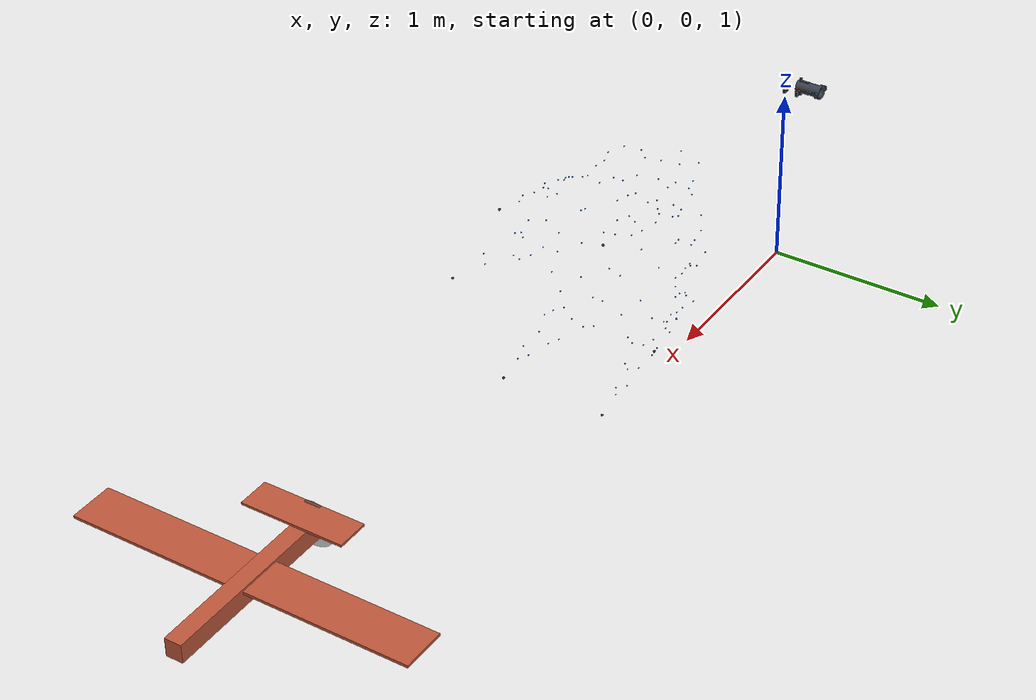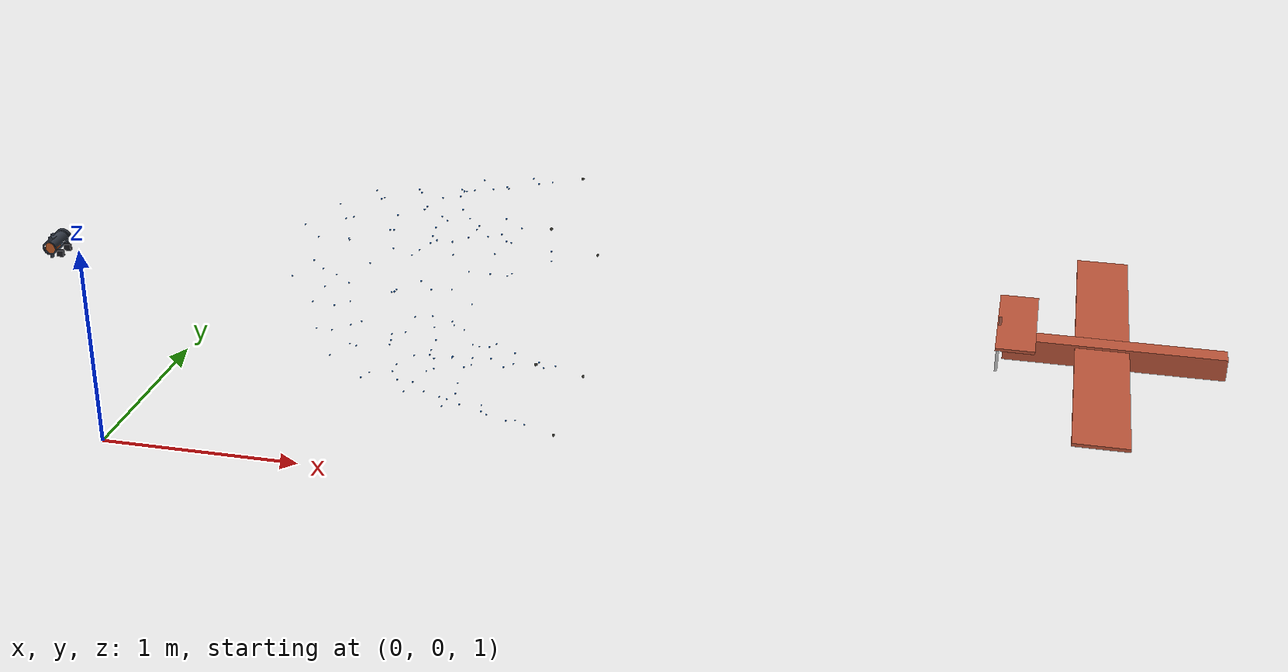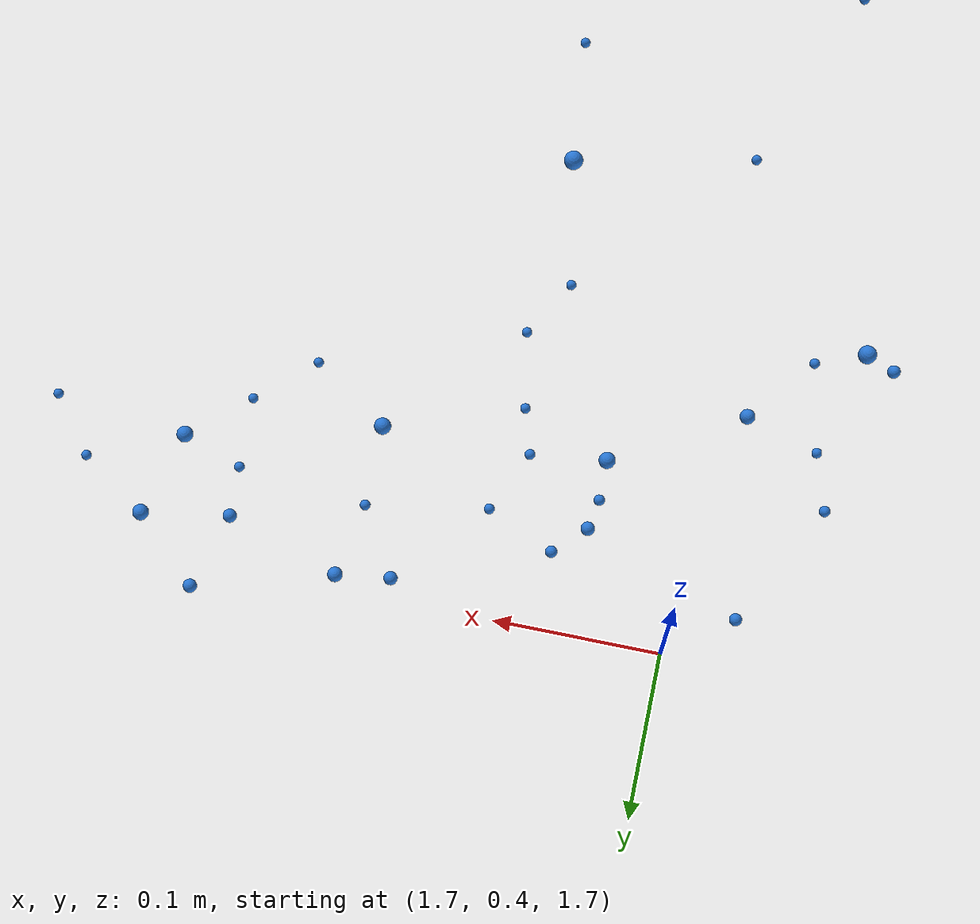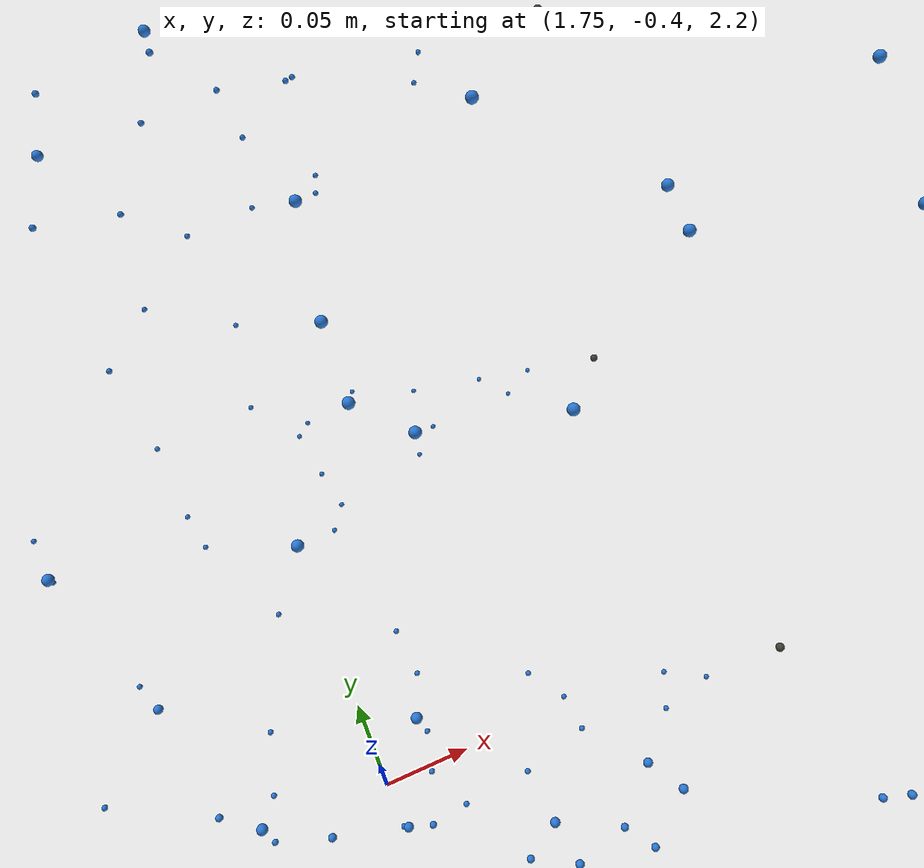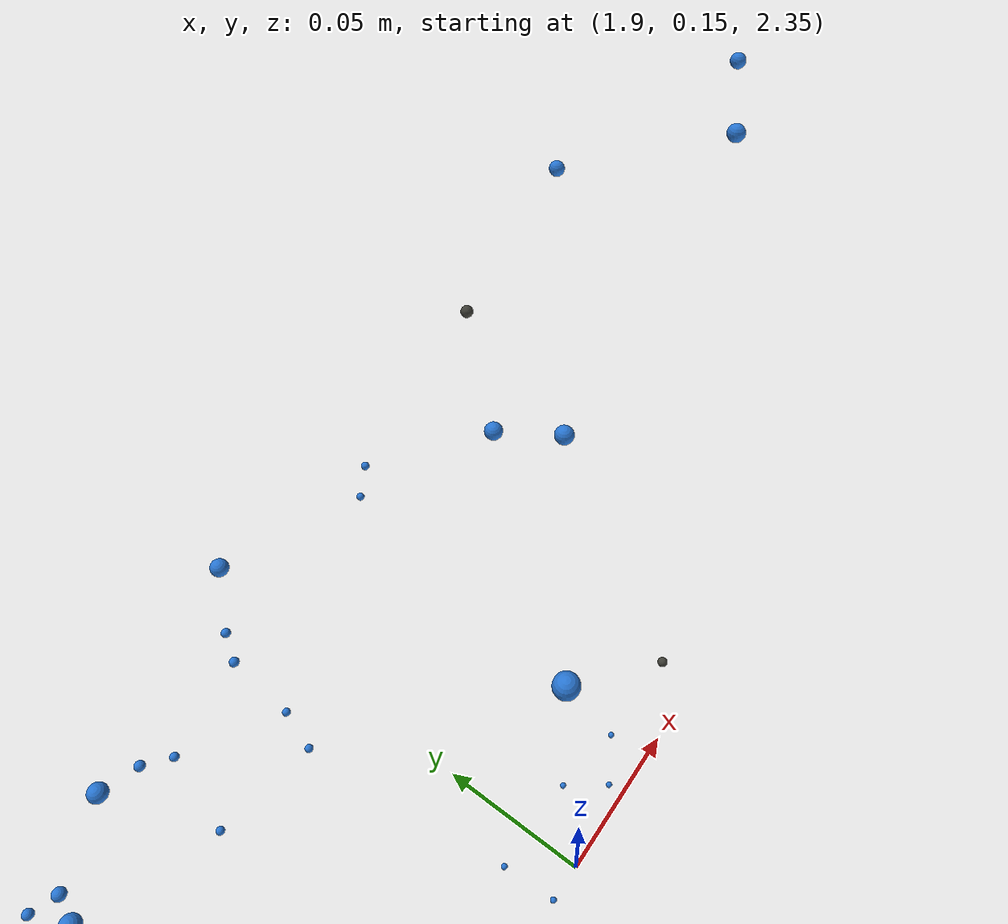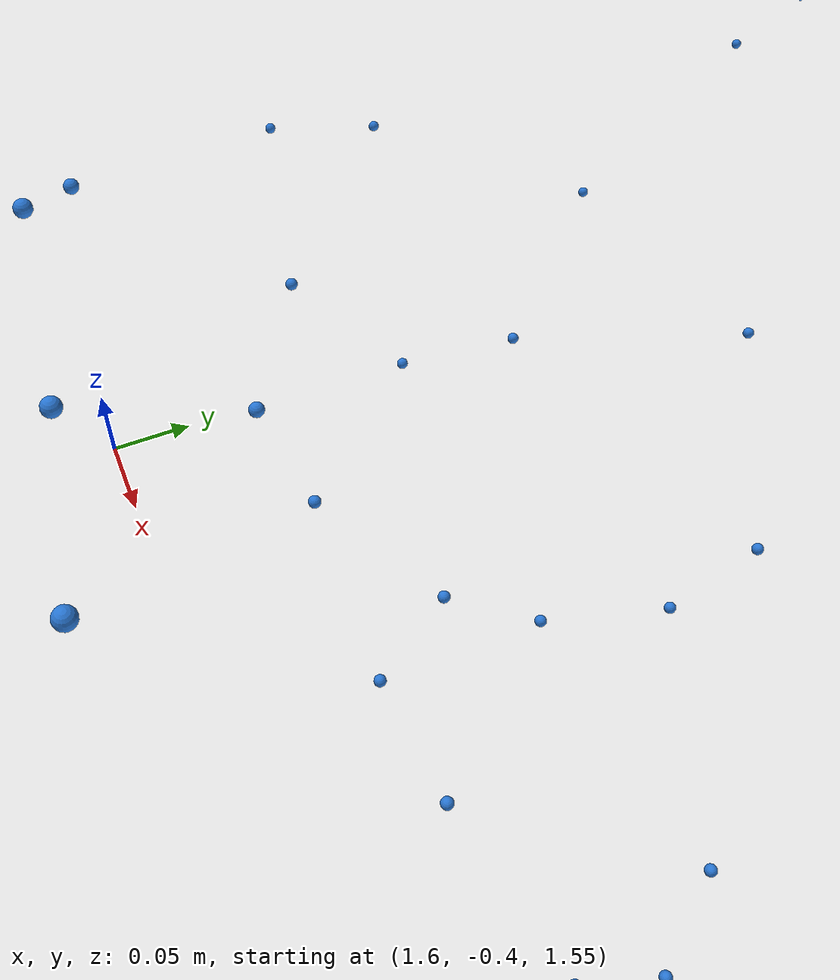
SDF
<?xml version="1.0" ?>
<sdf version="1.9">
  <world name="ag_atis">
    <physics name="hizli" type="dart">
      <max_step_size>0.000034</max_step_size>
      <!-- 0 = sinir yok: mumkun oldugunca hizli kos -->
      <real_time_factor>0</real_time_factor>
    </physics>
    <!-- Python modeli de yercekimini ucus eksenine DIK uygular -->
    <gravity>0 0 -9.81</gravity>

    <plugin filename="gz-sim-physics-system" name="gz::sim::systems::Physics"/>
    <plugin filename="gz-sim-user-commands-system"
            name="gz::sim::systems::UserCommands"/>
    <plugin filename="gz-sim-scene-broadcaster-system"
            name="gz::sim::systems::SceneBroadcaster"/>
    <plugin filename="gz-sim-contact-system"
            name="gz::sim::systems::Contact"/>

    <scene><ambient>0.85 0.85 0.85</ambient>
      <background>0.75 0.83 0.92</background><grid>false</grid></scene>
    <light type="directional" name="gunes">
      <pose>0 0 10 0 0 0</pose><diffuse>0.9 0.9 0.9 1</diffuse>
      <direction>-0.4 0.3 -0.9</direction></light>

    <include>
      <uri>model://ag_firlatici</uri>
      <name>ag_firlatici</name>
      <pose>-0.1498 0 2.0 0 0 0</pose>
    </include>
    <!-- firlaticiyi havada sabitle (test icin; gercekte drona baglanir) -->
    <joint name="firlatici_sabit" type="fixed">
      <parent>world</parent><child>ag_firlatici::namlu</child>
    </joint>

    <model name="m_dugum_0">
      <pose>1.84177 -0.43183 1.87464 0 0 0</pose>
      <link name="dugum_0">
        <pose>0 0 0 0 0 0</pose>
        <inertial><mass>4.919371e-06</mass><inertia>
          <ixx>2.410492e-11</ixx><iyy>2.410492e-11</iyy><izz>2.410492e-11</izz>
          <ixy>0</ixy><ixz>0</ixz><iyz>0</iyz></inertia></inertial>
        <visual name="v"><geometry><sphere><radius>0.00350</radius></sphere></geometry>
          <material><ambient>0.16 0.47 0.84 1</ambient><diffuse>0.16 0.47 0.84 1</diffuse></material></visual>
        <collision name="c"><geometry><sphere><radius>0.00350</radius></sphere></geometry>
          <surface><friction><ode><mu>1.2</mu><mu2>1.2</mu2></ode></friction>
            <contact><collide_bitmask>0x02</collide_bitmask>
              <ode><kp>1e5</kp><kd>10</kd></ode></contact></surface></collision>
      </link>
    </model>
    <model name="m_dugum_1">
      <pose>1.93743 -0.47093 1.91328 0 0 0</pose>
      <link name="dugum_1">
        <pose>0 0 0 0 0 0</pose>
        <inertial><mass>8.002209e-06</mass><inertia>
          <ixx>3.921082e-11</ixx><iyy>3.921082e-11</iyy><izz>3.921082e-11</izz>
          <ixy>0</ixy><ixz>0</ixz><iyz>0</iyz></inertia></inertial>
        <visual name="v"><geometry><sphere><radius>0.00350</radius></sphere></geometry>
          <material><ambient>0.16 0.47 0.84 1</ambient><diffuse>0.16 0.47 0.84 1</diffuse></material></visual>
        <collision name="c"><geometry><sphere><radius>0.00350</radius></sphere></geometry>
          <surface><friction><ode><mu>1.2</mu><mu2>1.2</mu2></ode></friction>
            <contact><collide_bitmask>0x02</collide_bitmask>
              <ode><kp>1e5</kp><kd>10</kd></ode></contact></surface></collision>
      </link>
    </model>
    <model name="m_dugum_2">
      <pose>1.86392 -0.46262 1.98043 0 0 0</pose>
      <link name="dugum_2">
        <pose>0 0 0 0 0 0</pose>
        <inertial><mass>8.771648e-06</mass><inertia>
          <ixx>4.298108e-11</ixx><iyy>4.298108e-11</iyy><izz>4.298108e-11</izz>
          <ixy>0</ixy><ixz>0</ixz><iyz>0</iyz></inertia></inertial>
        <visual name="v"><geometry><sphere><radius>0.00350</radius></sphere></geometry>
          <material><ambient>0.16 0.47 0.84 1</ambient><diffuse>0.16 0.47 0.84 1</diffuse></material></visual>
        <collision name="c"><geometry><sphere><radius>0.00350</radius></sphere></geometry>
          <surface><friction><ode><mu>1.2</mu><mu2>1.2</mu2></ode></friction>
            <contact><collide_bitmask>0x02</collide_bitmask>
              <ode><kp>1e5</kp><kd>10</kd></ode></contact></surface></collision>
      </link>
    </model>
    <model name="m_dugum_3">
      <pose>1.94461 -0.45572 2.05493 0 0 0</pose>
      <link name="dugum_3">
        <pose>0 0 0 0 0 0</pose>
        <inertial><mass>8.002209e-06</mass><inertia>
          <ixx>3.921082e-11</ixx><iyy>3.921082e-11</iyy><izz>3.921082e-11</izz>
          <ixy>0</ixy><ixz>0</ixz><iyz>0</iyz></inertia></inertial>
        <visual name="v"><geometry><sphere><radius>0.00350</radius></sphere></geometry>
          <material><ambient>0.16 0.47 0.84 1</ambient><diffuse>0.16 0.47 0.84 1</diffuse></material></visual>
        <collision name="c"><geometry><sphere><radius>0.00350</radius></sphere></geometry>
          <surface><friction><ode><mu>1.2</mu><mu2>1.2</mu2></ode></friction>
            <contact><collide_bitmask>0x02</collide_bitmask>
              <ode><kp>1e5</kp><kd>10</kd></ode></contact></surface></collision>
      </link>
    </model>
    <model name="m_dugum_4">
      <pose>1.84614 -0.44149 2.08017 0 0 0</pose>
      <link name="dugum_4">
        <pose>0 0 0 0 0 0</pose>
        <inertial><mass>4.919371e-06</mass><inertia>
          <ixx>2.410492e-11</ixx><iyy>2.410492e-11</iyy><izz>2.410492e-11</izz>
          <ixy>0</ixy><ixz>0</ixz><iyz>0</iyz></inertia></inertial>
        <visual name="v"><geometry><sphere><radius>0.00350</radius></sphere></geometry>
          <material><ambient>0.16 0.47 0.84 1</ambient><diffuse>0.16 0.47 0.84 1</diffuse></material></visual>
        <collision name="c"><geometry><sphere><radius>0.00350</radius></sphere></geometry>
          <surface><friction><ode><mu>1.2</mu><mu2>1.2</mu2></ode></friction>
            <contact><collide_bitmask>0x02</collide_bitmask>
              <ode><kp>1e5</kp><kd>10</kd></ode></contact></surface></collision>
      </link>
    </model>
    <model name="m_dugum_5">
      <pose>1.82744 -0.31192 1.57714 0 0 0</pose>
      <link name="dugum_5">
        <pose>0 0 0 0 0 0</pose>
        <inertial><mass>4.879748e-06</mass><inertia>
          <ixx>2.391077e-11</ixx><iyy>2.391077e-11</iyy><izz>2.391077e-11</izz>
          <ixy>0</ixy><ixz>0</ixz><iyz>0</iyz></inertia></inertial>
        <visual name="v"><geometry><sphere><radius>0.00350</radius></sphere></geometry>
          <material><ambient>0.16 0.47 0.84 1</ambient><diffuse>0.16 0.47 0.84 1</diffuse></material></visual>
        <collision name="c"><geometry><sphere><radius>0.00350</radius></sphere></geometry>
          <surface><friction><ode><mu>1.2</mu><mu2>1.2</mu2></ode></friction>
            <contact><collide_bitmask>0x02</collide_bitmask>
              <ode><kp>1e5</kp><kd>10</kd></ode></contact></surface></collision>
      </link>
    </model>
    <model name="m_dugum_6">
      <pose>1.75038 -0.31785 1.64452 0 0 0</pose>
      <link name="dugum_6">
        <pose>0 0 0 0 0 0</pose>
        <inertial><mass>7.725290e-06</mass><inertia>
          <ixx>3.785392e-11</ixx><iyy>3.785392e-11</iyy><izz>3.785392e-11</izz>
          <ixy>0</ixy><ixz>0</ixz><iyz>0</iyz></inertia></inertial>
        <visual name="v"><geometry><sphere><radius>0.00350</radius></sphere></geometry>
          <material><ambient>0.16 0.47 0.84 1</ambient><diffuse>0.16 0.47 0.84 1</diffuse></material></visual>
        <collision name="c"><geometry><sphere><radius>0.00350</radius></sphere></geometry>
          <surface><friction><ode><mu>1.2</mu><mu2>1.2</mu2></ode></friction>
            <contact><collide_bitmask>0x02</collide_bitmask>
              <ode><kp>1e5</kp><kd>10</kd></ode></contact></surface></collision>
      </link>
    </model>
    <model name="m_dugum_7">
      <pose>1.65809 -0.39346 1.80520 0 0 0</pose>
      <link name="dugum_7">
        <pose>0 0 0 0 0 0</pose>
        <inertial><mass>1.049795e-05</mass><inertia>
          <ixx>5.143998e-11</ixx><iyy>5.143998e-11</iyy><izz>5.143998e-11</izz>
          <ixy>0</ixy><ixz>0</ixz><iyz>0</iyz></inertia></inertial>
        <visual name="v"><geometry><sphere><radius>0.00350</radius></sphere></geometry>
          <material><ambient>0.16 0.47 0.84 1</ambient><diffuse>0.16 0.47 0.84 1</diffuse></material></visual>
        <collision name="c"><geometry><sphere><radius>0.00350</radius></sphere></geometry>
          <surface><friction><ode><mu>1.2</mu><mu2>1.2</mu2></ode></friction>
            <contact><collide_bitmask>0x02</collide_bitmask>
              <ode><kp>1e5</kp><kd>10</kd></ode></contact></surface></collision>
      </link>
    </model>
    <model name="m_dugum_8">
      <pose>1.74820 -0.41986 1.87269 0 0 0</pose>
      <link name="dugum_8">
        <pose>0 0 0 0 0 0</pose>
        <inertial><mass>8.082377e-06</mass><inertia>
          <ixx>3.960365e-11</ixx><iyy>3.960365e-11</iyy><izz>3.960365e-11</izz>
          <ixy>0</ixy><ixz>0</ixz><iyz>0</iyz></inertia></inertial>
        <visual name="v"><geometry><sphere><radius>0.00350</radius></sphere></geometry>
          <material><ambient>0.16 0.47 0.84 1</ambient><diffuse>0.16 0.47 0.84 1</diffuse></material></visual>
        <collision name="c"><geometry><sphere><radius>0.00350</radius></sphere></geometry>
          <surface><friction><ode><mu>1.2</mu><mu2>1.2</mu2></ode></friction>
            <contact><collide_bitmask>0x02</collide_bitmask>
              <ode><kp>1e5</kp><kd>10</kd></ode></contact></surface></collision>
      </link>
    </model>
    <model name="m_dugum_9">
      <pose>1.69446 -0.36078 1.94924 0 0 0</pose>
      <link name="dugum_9">
        <pose>0 0 0 0 0 0</pose>
        <inertial><mass>8.082377e-06</mass><inertia>
          <ixx>3.960365e-11</ixx><iyy>3.960365e-11</iyy><izz>3.960365e-11</izz>
          <ixy>0</ixy><ixz>0</ixz><iyz>0</iyz></inertia></inertial>
        <visual name="v"><geometry><sphere><radius>0.00350</radius></sphere></geometry>
          <material><ambient>0.16 0.47 0.84 1</ambient><diffuse>0.16 0.47 0.84 1</diffuse></material></visual>
        <collision name="c"><geometry><sphere><radius>0.00350</radius></sphere></geometry>
          <surface><friction><ode><mu>1.2</mu><mu2>1.2</mu2></ode></friction>
            <contact><collide_bitmask>0x02</collide_bitmask>
              <ode><kp>1e5</kp><kd>10</kd></ode></contact></surface></collision>
      </link>
    </model>
    <model name="m_dugum_10">
      <pose>1.75355 -0.39656 2.04435 0 0 0</pose>
      <link name="dugum_10">
        <pose>0 0 0 0 0 0</pose>
        <inertial><mass>8.082377e-06</mass><inertia>
          <ixx>3.960365e-11</ixx><iyy>3.960365e-11</iyy><izz>3.960365e-11</izz>
          <ixy>0</ixy><ixz>0</ixz><iyz>0</iyz></inertia></inertial>
        <visual name="v"><geometry><sphere><radius>0.00350</radius></sphere></geometry>
          <material><ambient>0.16 0.47 0.84 1</ambient><diffuse>0.16 0.47 0.84 1</diffuse></material></visual>
        <collision name="c"><geometry><sphere><radius>0.00350</radius></sphere></geometry>
          <surface><friction><ode><mu>1.2</mu><mu2>1.2</mu2></ode></friction>
            <contact><collide_bitmask>0x02</collide_bitmask>
              <ode><kp>1e5</kp><kd>10</kd></ode></contact></surface></collision>
      </link>
    </model>
    <model name="m_dugum_11">
      <pose>1.67196 -0.38384 2.16022 0 0 0</pose>
      <link name="dugum_11">
        <pose>0 0 0 0 0 0</pose>
        <inertial><mass>1.049795e-05</mass><inertia>
          <ixx>5.143998e-11</ixx><iyy>5.143998e-11</iyy><izz>5.143998e-11</izz>
          <ixy>0</ixy><ixz>0</ixz><iyz>0</iyz></inertia></inertial>
        <visual name="v"><geometry><sphere><radius>0.00350</radius></sphere></geometry>
          <material><ambient>0.16 0.47 0.84 1</ambient><diffuse>0.16 0.47 0.84 1</diffuse></material></visual>
        <collision name="c"><geometry><sphere><radius>0.00350</radius></sphere></geometry>
          <surface><friction><ode><mu>1.2</mu><mu2>1.2</mu2></ode></friction>
            <contact><collide_bitmask>0x02</collide_bitmask>
              <ode><kp>1e5</kp><kd>10</kd></ode></contact></surface></collision>
      </link>
    </model>
    <model name="m_dugum_12">
      <pose>1.74979 -0.29214 2.31108 0 0 0</pose>
      <link name="dugum_12">
        <pose>0 0 0 0 0 0</pose>
        <inertial><mass>7.725290e-06</mass><inertia>
          <ixx>3.785392e-11</ixx><iyy>3.785392e-11</iyy><izz>3.785392e-11</izz>
          <ixy>0</ixy><ixz>0</ixz><iyz>0</iyz></inertia></inertial>
        <visual name="v"><geometry><sphere><radius>0.00350</radius></sphere></geometry>
          <material><ambient>0.16 0.47 0.84 1</ambient><diffuse>0.16 0.47 0.84 1</diffuse></material></visual>
        <collision name="c"><geometry><sphere><radius>0.00350</radius></sphere></geometry>
          <surface><friction><ode><mu>1.2</mu><mu2>1.2</mu2></ode></friction>
            <contact><collide_bitmask>0x02</collide_bitmask>
              <ode><kp>1e5</kp><kd>10</kd></ode></contact></surface></collision>
      </link>
    </model>
    <model name="m_dugum_13">
      <pose>1.82584 -0.27926 2.35709 0 0 0</pose>
      <link name="dugum_13">
        <pose>0 0 0 0 0 0</pose>
        <inertial><mass>4.879748e-06</mass><inertia>
          <ixx>2.391077e-11</ixx><iyy>2.391077e-11</iyy><izz>2.391077e-11</izz>
          <ixy>0</ixy><ixz>0</ixz><iyz>0</iyz></inertia></inertial>
        <visual name="v"><geometry><sphere><radius>0.00350</radius></sphere></geometry>
          <material><ambient>0.16 0.47 0.84 1</ambient><diffuse>0.16 0.47 0.84 1</diffuse></material></visual>
        <collision name="c"><geometry><sphere><radius>0.00350</radius></sphere></geometry>
          <surface><friction><ode><mu>1.2</mu><mu2>1.2</mu2></ode></friction>
            <contact><collide_bitmask>0x02</collide_bitmask>
              <ode><kp>1e5</kp><kd>10</kd></ode></contact></surface></collision>
      </link>
    </model>
    <model name="m_dugum_14">
      <pose>2.19408 -0.28358 1.51469 0 0 0</pose>
      <link name="dugum_14">
        <pose>0 0 0 0 0 0</pose>
        <inertial><mass>5.409160e-06</mass><inertia>
          <ixx>2.650489e-11</ixx><iyy>2.650489e-11</iyy><izz>2.650489e-11</izz>
          <ixy>0</ixy><ixz>0</ixz><iyz>0</iyz></inertia></inertial>
        <visual name="v"><geometry><sphere><radius>0.00350</radius></sphere></geometry>
          <material><ambient>0.16 0.47 0.84 1</ambient><diffuse>0.16 0.47 0.84 1</diffuse></material></visual>
        <collision name="c"><geometry><sphere><radius>0.00350</radius></sphere></geometry>
          <surface><friction><ode><mu>1.2</mu><mu2>1.2</mu2></ode></friction>
            <contact><collide_bitmask>0x02</collide_bitmask>
              <ode><kp>1e5</kp><kd>10</kd></ode></contact></surface></collision>
      </link>
    </model>
    <model name="m_dugum_15">
      <pose>1.99882 -0.28525 1.55931 0 0 0</pose>
      <link name="dugum_15">
        <pose>0 0 0 0 0 0</pose>
        <inertial><mass>1.020561e-05</mass><inertia>
          <ixx>5.000751e-11</ixx><iyy>5.000751e-11</iyy><izz>5.000751e-11</izz>
          <ixy>0</ixy><ixz>0</ixz><iyz>0</iyz></inertia></inertial>
        <visual name="v"><geometry><sphere><radius>0.00350</radius></sphere></geometry>
          <material><ambient>0.16 0.47 0.84 1</ambient><diffuse>0.16 0.47 0.84 1</diffuse></material></visual>
        <collision name="c"><geometry><sphere><radius>0.00350</radius></sphere></geometry>
          <surface><friction><ode><mu>1.2</mu><mu2>1.2</mu2></ode></friction>
            <contact><collide_bitmask>0x02</collide_bitmask>
              <ode><kp>1e5</kp><kd>10</kd></ode></contact></surface></collision>
      </link>
    </model>
    <model name="m_dugum_16">
      <pose>1.80302 -0.26436 1.59584 0 0 0</pose>
      <link name="dugum_16">
        <pose>0 0 0 0 0 0</pose>
        <inertial><mass>8.082377e-06</mass><inertia>
          <ixx>3.960365e-11</ixx><iyy>3.960365e-11</iyy><izz>3.960365e-11</izz>
          <ixy>0</ixy><ixz>0</ixz><iyz>0</iyz></inertia></inertial>
        <visual name="v"><geometry><sphere><radius>0.00350</radius></sphere></geometry>
          <material><ambient>0.16 0.47 0.84 1</ambient><diffuse>0.16 0.47 0.84 1</diffuse></material></visual>
        <collision name="c"><geometry><sphere><radius>0.00350</radius></sphere></geometry>
          <surface><friction><ode><mu>1.2</mu><mu2>1.2</mu2></ode></friction>
            <contact><collide_bitmask>0x02</collide_bitmask>
              <ode><kp>1e5</kp><kd>10</kd></ode></contact></surface></collision>
      </link>
    </model>
    <model name="m_dugum_17">
      <pose>1.61646 -0.27995 1.66680 0 0 0</pose>
      <link name="dugum_17">
        <pose>0 0 0 0 0 0</pose>
        <inertial><mass>8.082377e-06</mass><inertia>
          <ixx>3.960365e-11</ixx><iyy>3.960365e-11</iyy><izz>3.960365e-11</izz>
          <ixy>0</ixy><ixz>0</ixz><iyz>0</iyz></inertia></inertial>
        <visual name="v"><geometry><sphere><radius>0.00350</radius></sphere></geometry>
          <material><ambient>0.16 0.47 0.84 1</ambient><diffuse>0.16 0.47 0.84 1</diffuse></material></visual>
        <collision name="c"><geometry><sphere><radius>0.00350</radius></sphere></geometry>
          <surface><friction><ode><mu>1.2</mu><mu2>1.2</mu2></ode></friction>
            <contact><collide_bitmask>0x02</collide_bitmask>
              <ode><kp>1e5</kp><kd>10</kd></ode></contact></surface></collision>
      </link>
    </model>
    <model name="m_dugum_18">
      <pose>1.60028 -0.28525 1.86349 0 0 0</pose>
      <link name="dugum_18">
        <pose>0 0 0 0 0 0</pose>
        <inertial><mass>8.082377e-06</mass><inertia>
          <ixx>3.960365e-11</ixx><iyy>3.960365e-11</iyy><izz>3.960365e-11</izz>
          <ixy>0</ixy><ixz>0</ixz><iyz>0</iyz></inertia></inertial>
        <visual name="v"><geometry><sphere><radius>0.00350</radius></sphere></geometry>
          <material><ambient>0.16 0.47 0.84 1</ambient><diffuse>0.16 0.47 0.84 1</diffuse></material></visual>
        <collision name="c"><geometry><sphere><radius>0.00350</radius></sphere></geometry>
          <surface><friction><ode><mu>1.2</mu><mu2>1.2</mu2></ode></friction>
            <contact><collide_bitmask>0x02</collide_bitmask>
              <ode><kp>1e5</kp><kd>10</kd></ode></contact></surface></collision>
      </link>
    </model>
    <model name="m_dugum_19">
      <pose>1.49622 -0.35414 1.97662 0 0 0</pose>
      <link name="dugum_19">
        <pose>0 0 0 0 0 0</pose>
        <inertial><mass>8.082377e-06</mass><inertia>
          <ixx>3.960365e-11</ixx><iyy>3.960365e-11</iyy><izz>3.960365e-11</izz>
          <ixy>0</ixy><ixz>0</ixz><iyz>0</iyz></inertia></inertial>
        <visual name="v"><geometry><sphere><radius>0.00350</radius></sphere></geometry>
          <material><ambient>0.16 0.47 0.84 1</ambient><diffuse>0.16 0.47 0.84 1</diffuse></material></visual>
        <collision name="c"><geometry><sphere><radius>0.00350</radius></sphere></geometry>
          <surface><friction><ode><mu>1.2</mu><mu2>1.2</mu2></ode></friction>
            <contact><collide_bitmask>0x02</collide_bitmask>
              <ode><kp>1e5</kp><kd>10</kd></ode></contact></surface></collision>
      </link>
    </model>
    <model name="m_dugum_20">
      <pose>1.61656 -0.25639 2.08534 0 0 0</pose>
      <link name="dugum_20">
        <pose>0 0 0 0 0 0</pose>
        <inertial><mass>8.082377e-06</mass><inertia>
          <ixx>3.960365e-11</ixx><iyy>3.960365e-11</iyy><izz>3.960365e-11</izz>
          <ixy>0</ixy><ixz>0</ixz><iyz>0</iyz></inertia></inertial>
        <visual name="v"><geometry><sphere><radius>0.00350</radius></sphere></geometry>
          <material><ambient>0.16 0.47 0.84 1</ambient><diffuse>0.16 0.47 0.84 1</diffuse></material></visual>
        <collision name="c"><geometry><sphere><radius>0.00350</radius></sphere></geometry>
          <surface><friction><ode><mu>1.2</mu><mu2>1.2</mu2></ode></friction>
            <contact><collide_bitmask>0x02</collide_bitmask>
              <ode><kp>1e5</kp><kd>10</kd></ode></contact></surface></collision>
      </link>
    </model>
    <model name="m_dugum_21">
      <pose>1.61635 -0.24094 2.28325 0 0 0</pose>
      <link name="dugum_21">
        <pose>0 0 0 0 0 0</pose>
        <inertial><mass>8.082377e-06</mass><inertia>
          <ixx>3.960365e-11</ixx><iyy>3.960365e-11</iyy><izz>3.960365e-11</izz>
          <ixy>0</ixy><ixz>0</ixz><iyz>0</iyz></inertia></inertial>
        <visual name="v"><geometry><sphere><radius>0.00350</radius></sphere></geometry>
          <material><ambient>0.16 0.47 0.84 1</ambient><diffuse>0.16 0.47 0.84 1</diffuse></material></visual>
        <collision name="c"><geometry><sphere><radius>0.00350</radius></sphere></geometry>
          <surface><friction><ode><mu>1.2</mu><mu2>1.2</mu2></ode></friction>
            <contact><collide_bitmask>0x02</collide_bitmask>
              <ode><kp>1e5</kp><kd>10</kd></ode></contact></surface></collision>
      </link>
    </model>
    <model name="m_dugum_22">
      <pose>1.79953 -0.25218 2.36375 0 0 0</pose>
      <link name="dugum_22">
        <pose>0 0 0 0 0 0</pose>
        <inertial><mass>8.082377e-06</mass><inertia>
          <ixx>3.960365e-11</ixx><iyy>3.960365e-11</iyy><izz>3.960365e-11</izz>
          <ixy>0</ixy><ixz>0</ixz><iyz>0</iyz></inertia></inertial>
        <visual name="v"><geometry><sphere><radius>0.00350</radius></sphere></geometry>
          <material><ambient>0.16 0.47 0.84 1</ambient><diffuse>0.16 0.47 0.84 1</diffuse></material></visual>
        <collision name="c"><geometry><sphere><radius>0.00350</radius></sphere></geometry>
          <surface><friction><ode><mu>1.2</mu><mu2>1.2</mu2></ode></friction>
            <contact><collide_bitmask>0x02</collide_bitmask>
              <ode><kp>1e5</kp><kd>10</kd></ode></contact></surface></collision>
      </link>
    </model>
    <model name="m_dugum_23">
      <pose>1.99456 -0.25461 2.41160 0 0 0</pose>
      <link name="dugum_23">
        <pose>0 0 0 0 0 0</pose>
        <inertial><mass>1.020561e-05</mass><inertia>
          <ixx>5.000751e-11</ixx><iyy>5.000751e-11</iyy><izz>5.000751e-11</izz>
          <ixy>0</ixy><ixz>0</ixz><iyz>0</iyz></inertia></inertial>
        <visual name="v"><geometry><sphere><radius>0.00350</radius></sphere></geometry>
          <material><ambient>0.16 0.47 0.84 1</ambient><diffuse>0.16 0.47 0.84 1</diffuse></material></visual>
        <collision name="c"><geometry><sphere><radius>0.00350</radius></sphere></geometry>
          <surface><friction><ode><mu>1.2</mu><mu2>1.2</mu2></ode></friction>
            <contact><collide_bitmask>0x02</collide_bitmask>
              <ode><kp>1e5</kp><kd>10</kd></ode></contact></surface></collision>
      </link>
    </model>
    <model name="m_dugum_24">
      <pose>2.19341 -0.26143 2.43976 0 0 0</pose>
      <link name="dugum_24">
        <pose>0 0 0 0 0 0</pose>
        <inertial><mass>5.409160e-06</mass><inertia>
          <ixx>2.650489e-11</ixx><iyy>2.650489e-11</iyy><izz>2.650489e-11</izz>
          <ixy>0</ixy><ixz>0</ixz><iyz>0</iyz></inertia></inertial>
        <visual name="v"><geometry><sphere><radius>0.00350</radius></sphere></geometry>
          <material><ambient>0.16 0.47 0.84 1</ambient><diffuse>0.16 0.47 0.84 1</diffuse></material></visual>
        <collision name="c"><geometry><sphere><radius>0.00350</radius></sphere></geometry>
          <surface><friction><ode><mu>1.2</mu><mu2>1.2</mu2></ode></friction>
            <contact><collide_bitmask>0x02</collide_bitmask>
              <ode><kp>1e5</kp><kd>10</kd></ode></contact></surface></collision>
      </link>
    </model>
    <model name="m_dugum_25">
      <pose>2.00550 -0.22829 1.51232 0 0 0</pose>
      <link name="dugum_25">
        <pose>0 0 0 0 0 0</pose>
        <inertial><mass>7.489365e-06</mass><inertia>
          <ixx>3.669789e-11</ixx><iyy>3.669789e-11</iyy><izz>3.669789e-11</izz>
          <ixy>0</ixy><ixz>0</ixz><iyz>0</iyz></inertia></inertial>
        <visual name="v"><geometry><sphere><radius>0.00350</radius></sphere></geometry>
          <material><ambient>0.16 0.47 0.84 1</ambient><diffuse>0.16 0.47 0.84 1</diffuse></material></visual>
        <collision name="c"><geometry><sphere><radius>0.00350</radius></sphere></geometry>
          <surface><friction><ode><mu>1.2</mu><mu2>1.2</mu2></ode></friction>
            <contact><collide_bitmask>0x02</collide_bitmask>
              <ode><kp>1e5</kp><kd>10</kd></ode></contact></surface></collision>
      </link>
    </model>
    <model name="m_dugum_26">
      <pose>1.81802 -0.20759 1.55622 0 0 0</pose>
      <link name="dugum_26">
        <pose>0 0 0 0 0 0</pose>
        <inertial><mass>1.143772e-05</mass><inertia>
          <ixx>5.604481e-11</ixx><iyy>5.604481e-11</iyy><izz>5.604481e-11</izz>
          <ixy>0</ixy><ixz>0</ixz><iyz>0</iyz></inertia></inertial>
        <visual name="v"><geometry><sphere><radius>0.00350</radius></sphere></geometry>
          <material><ambient>0.16 0.47 0.84 1</ambient><diffuse>0.16 0.47 0.84 1</diffuse></material></visual>
        <collision name="c"><geometry><sphere><radius>0.00350</radius></sphere></geometry>
          <surface><friction><ode><mu>1.2</mu><mu2>1.2</mu2></ode></friction>
            <contact><collide_bitmask>0x02</collide_bitmask>
              <ode><kp>1e5</kp><kd>10</kd></ode></contact></surface></collision>
      </link>
    </model>
    <model name="m_dugum_27">
      <pose>1.61847 -0.20678 1.57010 0 0 0</pose>
      <link name="dugum_27">
        <pose>0 0 0 0 0 0</pose>
        <inertial><mass>8.082377e-06</mass><inertia>
          <ixx>3.960365e-11</ixx><iyy>3.960365e-11</iyy><izz>3.960365e-11</izz>
          <ixy>0</ixy><ixz>0</ixz><iyz>0</iyz></inertia></inertial>
        <visual name="v"><geometry><sphere><radius>0.00350</radius></sphere></geometry>
          <material><ambient>0.16 0.47 0.84 1</ambient><diffuse>0.16 0.47 0.84 1</diffuse></material></visual>
        <collision name="c"><geometry><sphere><radius>0.00350</radius></sphere></geometry>
          <surface><friction><ode><mu>1.2</mu><mu2>1.2</mu2></ode></friction>
            <contact><collide_bitmask>0x02</collide_bitmask>
              <ode><kp>1e5</kp><kd>10</kd></ode></contact></surface></collision>
      </link>
    </model>
    <model name="m_dugum_28">
      <pose>1.42858 -0.22729 1.62974 0 0 0</pose>
      <link name="dugum_28">
        <pose>0 0 0 0 0 0</pose>
        <inertial><mass>8.082377e-06</mass><inertia>
          <ixx>3.960365e-11</ixx><iyy>3.960365e-11</iyy><izz>3.960365e-11</izz>
          <ixy>0</ixy><ixz>0</ixz><iyz>0</iyz></inertia></inertial>
        <visual name="v"><geometry><sphere><radius>0.00350</radius></sphere></geometry>
          <material><ambient>0.16 0.47 0.84 1</ambient><diffuse>0.16 0.47 0.84 1</diffuse></material></visual>
        <collision name="c"><geometry><sphere><radius>0.00350</radius></sphere></geometry>
          <surface><friction><ode><mu>1.2</mu><mu2>1.2</mu2></ode></friction>
            <contact><collide_bitmask>0x02</collide_bitmask>
              <ode><kp>1e5</kp><kd>10</kd></ode></contact></surface></collision>
      </link>
    </model>
    <model name="m_dugum_29">
      <pose>1.40511 -0.27713 1.82005 0 0 0</pose>
      <link name="dugum_29">
        <pose>0 0 0 0 0 0</pose>
        <inertial><mass>8.082377e-06</mass><inertia>
          <ixx>3.960365e-11</ixx><iyy>3.960365e-11</iyy><izz>3.960365e-11</izz>
          <ixy>0</ixy><ixz>0</ixz><iyz>0</iyz></inertia></inertial>
        <visual name="v"><geometry><sphere><radius>0.00350</radius></sphere></geometry>
          <material><ambient>0.16 0.47 0.84 1</ambient><diffuse>0.16 0.47 0.84 1</diffuse></material></visual>
        <collision name="c"><geometry><sphere><radius>0.00350</radius></sphere></geometry>
          <surface><friction><ode><mu>1.2</mu><mu2>1.2</mu2></ode></friction>
            <contact><collide_bitmask>0x02</collide_bitmask>
              <ode><kp>1e5</kp><kd>10</kd></ode></contact></surface></collision>
      </link>
    </model>
    <model name="m_dugum_30">
      <pose>1.33048 -0.24177 1.98270 0 0 0</pose>
      <link name="dugum_30">
        <pose>0 0 0 0 0 0</pose>
        <inertial><mass>8.082377e-06</mass><inertia>
          <ixx>3.960365e-11</ixx><iyy>3.960365e-11</iyy><izz>3.960365e-11</izz>
          <ixy>0</ixy><ixz>0</ixz><iyz>0</iyz></inertia></inertial>
        <visual name="v"><geometry><sphere><radius>0.00350</radius></sphere></geometry>
          <material><ambient>0.16 0.47 0.84 1</ambient><diffuse>0.16 0.47 0.84 1</diffuse></material></visual>
        <collision name="c"><geometry><sphere><radius>0.00350</radius></sphere></geometry>
          <surface><friction><ode><mu>1.2</mu><mu2>1.2</mu2></ode></friction>
            <contact><collide_bitmask>0x02</collide_bitmask>
              <ode><kp>1e5</kp><kd>10</kd></ode></contact></surface></collision>
      </link>
    </model>
    <model name="m_dugum_31">
      <pose>1.42270 -0.29064 2.12137 0 0 0</pose>
      <link name="dugum_31">
        <pose>0 0 0 0 0 0</pose>
        <inertial><mass>8.082377e-06</mass><inertia>
          <ixx>3.960365e-11</ixx><iyy>3.960365e-11</iyy><izz>3.960365e-11</izz>
          <ixy>0</ixy><ixz>0</ixz><iyz>0</iyz></inertia></inertial>
        <visual name="v"><geometry><sphere><radius>0.00350</radius></sphere></geometry>
          <material><ambient>0.16 0.47 0.84 1</ambient><diffuse>0.16 0.47 0.84 1</diffuse></material></visual>
        <collision name="c"><geometry><sphere><radius>0.00350</radius></sphere></geometry>
          <surface><friction><ode><mu>1.2</mu><mu2>1.2</mu2></ode></friction>
            <contact><collide_bitmask>0x02</collide_bitmask>
              <ode><kp>1e5</kp><kd>10</kd></ode></contact></surface></collision>
      </link>
    </model>
    <model name="m_dugum_32">
      <pose>1.41851 -0.24448 2.31207 0 0 0</pose>
      <link name="dugum_32">
        <pose>0 0 0 0 0 0</pose>
        <inertial><mass>8.082377e-06</mass><inertia>
          <ixx>3.960365e-11</ixx><iyy>3.960365e-11</iyy><izz>3.960365e-11</izz>
          <ixy>0</ixy><ixz>0</ixz><iyz>0</iyz></inertia></inertial>
        <visual name="v"><geometry><sphere><radius>0.00350</radius></sphere></geometry>
          <material><ambient>0.16 0.47 0.84 1</ambient><diffuse>0.16 0.47 0.84 1</diffuse></material></visual>
        <collision name="c"><geometry><sphere><radius>0.00350</radius></sphere></geometry>
          <surface><friction><ode><mu>1.2</mu><mu2>1.2</mu2></ode></friction>
            <contact><collide_bitmask>0x02</collide_bitmask>
              <ode><kp>1e5</kp><kd>10</kd></ode></contact></surface></collision>
      </link>
    </model>
    <model name="m_dugum_33">
      <pose>1.60748 -0.19765 2.34865 0 0 0</pose>
      <link name="dugum_33">
        <pose>0 0 0 0 0 0</pose>
        <inertial><mass>8.082377e-06</mass><inertia>
          <ixx>3.960365e-11</ixx><iyy>3.960365e-11</iyy><izz>3.960365e-11</izz>
          <ixy>0</ixy><ixz>0</ixz><iyz>0</iyz></inertia></inertial>
        <visual name="v"><geometry><sphere><radius>0.00350</radius></sphere></geometry>
          <material><ambient>0.16 0.47 0.84 1</ambient><diffuse>0.16 0.47 0.84 1</diffuse></material></visual>
        <collision name="c"><geometry><sphere><radius>0.00350</radius></sphere></geometry>
          <surface><friction><ode><mu>1.2</mu><mu2>1.2</mu2></ode></friction>
            <contact><collide_bitmask>0x02</collide_bitmask>
              <ode><kp>1e5</kp><kd>10</kd></ode></contact></surface></collision>
      </link>
    </model>
    <model name="m_dugum_34">
      <pose>1.80139 -0.21116 2.38395 0 0 0</pose>
      <link name="dugum_34">
        <pose>0 0 0 0 0 0</pose>
        <inertial><mass>1.139144e-05</mass><inertia>
          <ixx>5.581805e-11</ixx><iyy>5.581805e-11</iyy><izz>5.581805e-11</izz>
          <ixy>0</ixy><ixz>0</ixz><iyz>0</iyz></inertia></inertial>
        <visual name="v"><geometry><sphere><radius>0.00350</radius></sphere></geometry>
          <material><ambient>0.16 0.47 0.84 1</ambient><diffuse>0.16 0.47 0.84 1</diffuse></material></visual>
        <collision name="c"><geometry><sphere><radius>0.00350</radius></sphere></geometry>
          <surface><friction><ode><mu>1.2</mu><mu2>1.2</mu2></ode></friction>
            <contact><collide_bitmask>0x02</collide_bitmask>
              <ode><kp>1e5</kp><kd>10</kd></ode></contact></surface></collision>
      </link>
    </model>
    <model name="m_dugum_35">
      <pose>1.99722 -0.22541 2.41762 0 0 0</pose>
      <link name="dugum_35">
        <pose>0 0 0 0 0 0</pose>
        <inertial><mass>7.376919e-06</mass><inertia>
          <ixx>3.614690e-11</ixx><iyy>3.614690e-11</iyy><izz>3.614690e-11</izz>
          <ixy>0</ixy><ixz>0</ixz><iyz>0</iyz></inertia></inertial>
        <visual name="v"><geometry><sphere><radius>0.00350</radius></sphere></geometry>
          <material><ambient>0.16 0.47 0.84 1</ambient><diffuse>0.16 0.47 0.84 1</diffuse></material></visual>
        <collision name="c"><geometry><sphere><radius>0.00350</radius></sphere></geometry>
          <surface><friction><ode><mu>1.2</mu><mu2>1.2</mu2></ode></friction>
            <contact><collide_bitmask>0x02</collide_bitmask>
              <ode><kp>1e5</kp><kd>10</kd></ode></contact></surface></collision>
      </link>
    </model>
    <model name="m_dugum_36">
      <pose>1.83472 -0.12988 1.54742 0 0 0</pose>
      <link name="dugum_36">
        <pose>0 0 0 0 0 0</pose>
        <inertial><mass>7.560548e-06</mass><inertia>
          <ixx>3.704669e-11</ixx><iyy>3.704669e-11</iyy><izz>3.704669e-11</izz>
          <ixy>0</ixy><ixz>0</ixz><iyz>0</iyz></inertia></inertial>
        <visual name="v"><geometry><sphere><radius>0.00350</radius></sphere></geometry>
          <material><ambient>0.16 0.47 0.84 1</ambient><diffuse>0.16 0.47 0.84 1</diffuse></material></visual>
        <collision name="c"><geometry><sphere><radius>0.00350</radius></sphere></geometry>
          <surface><friction><ode><mu>1.2</mu><mu2>1.2</mu2></ode></friction>
            <contact><collide_bitmask>0x02</collide_bitmask>
              <ode><kp>1e5</kp><kd>10</kd></ode></contact></surface></collision>
      </link>
    </model>
    <model name="m_dugum_37">
      <pose>1.63825 -0.13751 1.58584 0 0 0</pose>
      <link name="dugum_37">
        <pose>0 0 0 0 0 0</pose>
        <inertial><mass>8.082377e-06</mass><inertia>
          <ixx>3.960365e-11</ixx><iyy>3.960365e-11</iyy><izz>3.960365e-11</izz>
          <ixy>0</ixy><ixz>0</ixz><iyz>0</iyz></inertia></inertial>
        <visual name="v"><geometry><sphere><radius>0.00350</radius></sphere></geometry>
          <material><ambient>0.16 0.47 0.84 1</ambient><diffuse>0.16 0.47 0.84 1</diffuse></material></visual>
        <collision name="c"><geometry><sphere><radius>0.00350</radius></sphere></geometry>
          <surface><friction><ode><mu>1.2</mu><mu2>1.2</mu2></ode></friction>
            <contact><collide_bitmask>0x02</collide_bitmask>
              <ode><kp>1e5</kp><kd>10</kd></ode></contact></surface></collision>
      </link>
    </model>
    <model name="m_dugum_38">
      <pose>1.44161 -0.15365 1.61991 0 0 0</pose>
      <link name="dugum_38">
        <pose>0 0 0 0 0 0</pose>
        <inertial><mass>8.082377e-06</mass><inertia>
          <ixx>3.960365e-11</ixx><iyy>3.960365e-11</iyy><izz>3.960365e-11</izz>
          <ixy>0</ixy><ixz>0</ixz><iyz>0</iyz></inertia></inertial>
        <visual name="v"><geometry><sphere><radius>0.00350</radius></sphere></geometry>
          <material><ambient>0.16 0.47 0.84 1</ambient><diffuse>0.16 0.47 0.84 1</diffuse></material></visual>
        <collision name="c"><geometry><sphere><radius>0.00350</radius></sphere></geometry>
          <surface><friction><ode><mu>1.2</mu><mu2>1.2</mu2></ode></friction>
            <contact><collide_bitmask>0x02</collide_bitmask>
              <ode><kp>1e5</kp><kd>10</kd></ode></contact></surface></collision>
      </link>
    </model>
    <model name="m_dugum_39">
      <pose>1.25490 -0.14082 1.67847 0 0 0</pose>
      <link name="dugum_39">
        <pose>0 0 0 0 0 0</pose>
        <inertial><mass>8.082377e-06</mass><inertia>
          <ixx>3.960365e-11</ixx><iyy>3.960365e-11</iyy><izz>3.960365e-11</izz>
          <ixy>0</ixy><ixz>0</ixz><iyz>0</iyz></inertia></inertial>
        <visual name="v"><geometry><sphere><radius>0.00350</radius></sphere></geometry>
          <material><ambient>0.16 0.47 0.84 1</ambient><diffuse>0.16 0.47 0.84 1</diffuse></material></visual>
        <collision name="c"><geometry><sphere><radius>0.00350</radius></sphere></geometry>
          <surface><friction><ode><mu>1.2</mu><mu2>1.2</mu2></ode></friction>
            <contact><collide_bitmask>0x02</collide_bitmask>
              <ode><kp>1e5</kp><kd>10</kd></ode></contact></surface></collision>
      </link>
    </model>
    <model name="m_dugum_40">
      <pose>1.26754 -0.13281 1.80291 0 0 0</pose>
      <link name="dugum_40">
        <pose>0 0 0 0 0 0</pose>
        <inertial><mass>8.082377e-06</mass><inertia>
          <ixx>3.960365e-11</ixx><iyy>3.960365e-11</iyy><izz>3.960365e-11</izz>
          <ixy>0</ixy><ixz>0</ixz><iyz>0</iyz></inertia></inertial>
        <visual name="v"><geometry><sphere><radius>0.00350</radius></sphere></geometry>
          <material><ambient>0.16 0.47 0.84 1</ambient><diffuse>0.16 0.47 0.84 1</diffuse></material></visual>
        <collision name="c"><geometry><sphere><radius>0.00350</radius></sphere></geometry>
          <surface><friction><ode><mu>1.2</mu><mu2>1.2</mu2></ode></friction>
            <contact><collide_bitmask>0x02</collide_bitmask>
              <ode><kp>1e5</kp><kd>10</kd></ode></contact></surface></collision>
      </link>
    </model>
    <model name="m_dugum_41">
      <pose>1.22473 -0.07167 1.98462 0 0 0</pose>
      <link name="dugum_41">
        <pose>0 0 0 0 0 0</pose>
        <inertial><mass>8.082377e-06</mass><inertia>
          <ixx>3.960365e-11</ixx><iyy>3.960365e-11</iyy><izz>3.960365e-11</izz>
          <ixy>0</ixy><ixz>0</ixz><iyz>0</iyz></inertia></inertial>
        <visual name="v"><geometry><sphere><radius>0.00350</radius></sphere></geometry>
          <material><ambient>0.16 0.47 0.84 1</ambient><diffuse>0.16 0.47 0.84 1</diffuse></material></visual>
        <collision name="c"><geometry><sphere><radius>0.00350</radius></sphere></geometry>
          <surface><friction><ode><mu>1.2</mu><mu2>1.2</mu2></ode></friction>
            <contact><collide_bitmask>0x02</collide_bitmask>
              <ode><kp>1e5</kp><kd>10</kd></ode></contact></surface></collision>
      </link>
    </model>
    <model name="m_dugum_42">
      <pose>1.26251 -0.17043 2.11993 0 0 0</pose>
      <link name="dugum_42">
        <pose>0 0 0 0 0 0</pose>
        <inertial><mass>8.082377e-06</mass><inertia>
          <ixx>3.960365e-11</ixx><iyy>3.960365e-11</iyy><izz>3.960365e-11</izz>
          <ixy>0</ixy><ixz>0</ixz><iyz>0</iyz></inertia></inertial>
        <visual name="v"><geometry><sphere><radius>0.00350</radius></sphere></geometry>
          <material><ambient>0.16 0.47 0.84 1</ambient><diffuse>0.16 0.47 0.84 1</diffuse></material></visual>
        <collision name="c"><geometry><sphere><radius>0.00350</radius></sphere></geometry>
          <surface><friction><ode><mu>1.2</mu><mu2>1.2</mu2></ode></friction>
            <contact><collide_bitmask>0x02</collide_bitmask>
              <ode><kp>1e5</kp><kd>10</kd></ode></contact></surface></collision>
      </link>
    </model>
    <model name="m_dugum_43">
      <pose>1.24515 -0.15702 2.26447 0 0 0</pose>
      <link name="dugum_43">
        <pose>0 0 0 0 0 0</pose>
        <inertial><mass>8.082377e-06</mass><inertia>
          <ixx>3.960365e-11</ixx><iyy>3.960365e-11</iyy><izz>3.960365e-11</izz>
          <ixy>0</ixy><ixz>0</ixz><iyz>0</iyz></inertia></inertial>
        <visual name="v"><geometry><sphere><radius>0.00350</radius></sphere></geometry>
          <material><ambient>0.16 0.47 0.84 1</ambient><diffuse>0.16 0.47 0.84 1</diffuse></material></visual>
        <collision name="c"><geometry><sphere><radius>0.00350</radius></sphere></geometry>
          <surface><friction><ode><mu>1.2</mu><mu2>1.2</mu2></ode></friction>
            <contact><collide_bitmask>0x02</collide_bitmask>
              <ode><kp>1e5</kp><kd>10</kd></ode></contact></surface></collision>
      </link>
    </model>
    <model name="m_dugum_44">
      <pose>1.41319 -0.15646 2.37346 0 0 0</pose>
      <link name="dugum_44">
        <pose>0 0 0 0 0 0</pose>
        <inertial><mass>8.082377e-06</mass><inertia>
          <ixx>3.960365e-11</ixx><iyy>3.960365e-11</iyy><izz>3.960365e-11</izz>
          <ixy>0</ixy><ixz>0</ixz><iyz>0</iyz></inertia></inertial>
        <visual name="v"><geometry><sphere><radius>0.00350</radius></sphere></geometry>
          <material><ambient>0.16 0.47 0.84 1</ambient><diffuse>0.16 0.47 0.84 1</diffuse></material></visual>
        <collision name="c"><geometry><sphere><radius>0.00350</radius></sphere></geometry>
          <surface><friction><ode><mu>1.2</mu><mu2>1.2</mu2></ode></friction>
            <contact><collide_bitmask>0x02</collide_bitmask>
              <ode><kp>1e5</kp><kd>10</kd></ode></contact></surface></collision>
      </link>
    </model>
    <model name="m_dugum_45">
      <pose>1.61183 -0.14912 2.39835 0 0 0</pose>
      <link name="dugum_45">
        <pose>0 0 0 0 0 0</pose>
        <inertial><mass>8.082377e-06</mass><inertia>
          <ixx>3.960365e-11</ixx><iyy>3.960365e-11</iyy><izz>3.960365e-11</izz>
          <ixy>0</ixy><ixz>0</ixz><iyz>0</iyz></inertia></inertial>
        <visual name="v"><geometry><sphere><radius>0.00350</radius></sphere></geometry>
          <material><ambient>0.16 0.47 0.84 1</ambient><diffuse>0.16 0.47 0.84 1</diffuse></material></visual>
        <collision name="c"><geometry><sphere><radius>0.00350</radius></sphere></geometry>
          <surface><friction><ode><mu>1.2</mu><mu2>1.2</mu2></ode></friction>
            <contact><collide_bitmask>0x02</collide_bitmask>
              <ode><kp>1e5</kp><kd>10</kd></ode></contact></surface></collision>
      </link>
    </model>
    <model name="m_dugum_46">
      <pose>1.81185 -0.14880 2.41141 0 0 0</pose>
      <link name="dugum_46">
        <pose>0 0 0 0 0 0</pose>
        <inertial><mass>7.344173e-06</mass><inertia>
          <ixx>3.598645e-11</ixx><iyy>3.598645e-11</iyy><izz>3.598645e-11</izz>
          <ixy>0</ixy><ixz>0</ixz><iyz>0</iyz></inertia></inertial>
        <visual name="v"><geometry><sphere><radius>0.00350</radius></sphere></geometry>
          <material><ambient>0.16 0.47 0.84 1</ambient><diffuse>0.16 0.47 0.84 1</diffuse></material></visual>
        <collision name="c"><geometry><sphere><radius>0.00350</radius></sphere></geometry>
          <surface><friction><ode><mu>1.2</mu><mu2>1.2</mu2></ode></friction>
            <contact><collide_bitmask>0x02</collide_bitmask>
              <ode><kp>1e5</kp><kd>10</kd></ode></contact></surface></collision>
      </link>
    </model>
    <model name="m_dugum_47">
      <pose>1.69309 0.00601 1.58740 0 0 0</pose>
      <link name="dugum_47">
        <pose>0 0 0 0 0 0</pose>
        <inertial><mass>7.641740e-06</mass><inertia>
          <ixx>3.744453e-11</ixx><iyy>3.744453e-11</iyy><izz>3.744453e-11</izz>
          <ixy>0</ixy><ixz>0</ixz><iyz>0</iyz></inertia></inertial>
        <visual name="v"><geometry><sphere><radius>0.00350</radius></sphere></geometry>
          <material><ambient>0.16 0.47 0.84 1</ambient><diffuse>0.16 0.47 0.84 1</diffuse></material></visual>
        <collision name="c"><geometry><sphere><radius>0.00350</radius></sphere></geometry>
          <surface><friction><ode><mu>1.2</mu><mu2>1.2</mu2></ode></friction>
            <contact><collide_bitmask>0x02</collide_bitmask>
              <ode><kp>1e5</kp><kd>10</kd></ode></contact></surface></collision>
      </link>
    </model>
    <model name="m_dugum_48">
      <pose>1.49589 -0.00063 1.55382 0 0 0</pose>
      <link name="dugum_48">
        <pose>0 0 0 0 0 0</pose>
        <inertial><mass>8.082377e-06</mass><inertia>
          <ixx>3.960365e-11</ixx><iyy>3.960365e-11</iyy><izz>3.960365e-11</izz>
          <ixy>0</ixy><ixz>0</ixz><iyz>0</iyz></inertia></inertial>
        <visual name="v"><geometry><sphere><radius>0.00350</radius></sphere></geometry>
          <material><ambient>0.16 0.47 0.84 1</ambient><diffuse>0.16 0.47 0.84 1</diffuse></material></visual>
        <collision name="c"><geometry><sphere><radius>0.00350</radius></sphere></geometry>
          <surface><friction><ode><mu>1.2</mu><mu2>1.2</mu2></ode></friction>
            <contact><collide_bitmask>0x02</collide_bitmask>
              <ode><kp>1e5</kp><kd>10</kd></ode></contact></surface></collision>
      </link>
    </model>
    <model name="m_dugum_49">
      <pose>1.32727 0.00531 1.66146 0 0 0</pose>
      <link name="dugum_49">
        <pose>0 0 0 0 0 0</pose>
        <inertial><mass>8.082377e-06</mass><inertia>
          <ixx>3.960365e-11</ixx><iyy>3.960365e-11</iyy><izz>3.960365e-11</izz>
          <ixy>0</ixy><ixz>0</ixz><iyz>0</iyz></inertia></inertial>
        <visual name="v"><geometry><sphere><radius>0.00350</radius></sphere></geometry>
          <material><ambient>0.16 0.47 0.84 1</ambient><diffuse>0.16 0.47 0.84 1</diffuse></material></visual>
        <collision name="c"><geometry><sphere><radius>0.00350</radius></sphere></geometry>
          <surface><friction><ode><mu>1.2</mu><mu2>1.2</mu2></ode></friction>
            <contact><collide_bitmask>0x02</collide_bitmask>
              <ode><kp>1e5</kp><kd>10</kd></ode></contact></surface></collision>
      </link>
    </model>
    <model name="m_dugum_50">
      <pose>1.13849 0.01027 1.72832 0 0 0</pose>
      <link name="dugum_50">
        <pose>0 0 0 0 0 0</pose>
        <inertial><mass>8.082377e-06</mass><inertia>
          <ixx>3.960365e-11</ixx><iyy>3.960365e-11</iyy><izz>3.960365e-11</izz>
          <ixy>0</ixy><ixz>0</ixz><iyz>0</iyz></inertia></inertial>
        <visual name="v"><geometry><sphere><radius>0.00350</radius></sphere></geometry>
          <material><ambient>0.16 0.47 0.84 1</ambient><diffuse>0.16 0.47 0.84 1</diffuse></material></visual>
        <collision name="c"><geometry><sphere><radius>0.00350</radius></sphere></geometry>
          <surface><friction><ode><mu>1.2</mu><mu2>1.2</mu2></ode></friction>
            <contact><collide_bitmask>0x02</collide_bitmask>
              <ode><kp>1e5</kp><kd>10</kd></ode></contact></surface></collision>
      </link>
    </model>
    <model name="m_dugum_51">
      <pose>1.13302 0.00161 1.86529 0 0 0</pose>
      <link name="dugum_51">
        <pose>0 0 0 0 0 0</pose>
        <inertial><mass>8.082377e-06</mass><inertia>
          <ixx>3.960365e-11</ixx><iyy>3.960365e-11</iyy><izz>3.960365e-11</izz>
          <ixy>0</ixy><ixz>0</ixz><iyz>0</iyz></inertia></inertial>
        <visual name="v"><geometry><sphere><radius>0.00350</radius></sphere></geometry>
          <material><ambient>0.16 0.47 0.84 1</ambient><diffuse>0.16 0.47 0.84 1</diffuse></material></visual>
        <collision name="c"><geometry><sphere><radius>0.00350</radius></sphere></geometry>
          <surface><friction><ode><mu>1.2</mu><mu2>1.2</mu2></ode></friction>
            <contact><collide_bitmask>0x02</collide_bitmask>
              <ode><kp>1e5</kp><kd>10</kd></ode></contact></surface></collision>
      </link>
    </model>
    <model name="m_dugum_52">
      <pose>1.04025 0.00569 1.98206 0 0 0</pose>
      <link name="dugum_52">
        <pose>0 0 0 0 0 0</pose>
        <inertial><mass>8.082377e-06</mass><inertia>
          <ixx>3.960365e-11</ixx><iyy>3.960365e-11</iyy><izz>3.960365e-11</izz>
          <ixy>0</ixy><ixz>0</ixz><iyz>0</iyz></inertia></inertial>
        <visual name="v"><geometry><sphere><radius>0.00350</radius></sphere></geometry>
          <material><ambient>0.16 0.47 0.84 1</ambient><diffuse>0.16 0.47 0.84 1</diffuse></material></visual>
        <collision name="c"><geometry><sphere><radius>0.00350</radius></sphere></geometry>
          <surface><friction><ode><mu>1.2</mu><mu2>1.2</mu2></ode></friction>
            <contact><collide_bitmask>0x02</collide_bitmask>
              <ode><kp>1e5</kp><kd>10</kd></ode></contact></surface></collision>
      </link>
    </model>
    <model name="m_dugum_53">
      <pose>1.15659 -0.00594 2.07665 0 0 0</pose>
      <link name="dugum_53">
        <pose>0 0 0 0 0 0</pose>
        <inertial><mass>8.082377e-06</mass><inertia>
          <ixx>3.960365e-11</ixx><iyy>3.960365e-11</iyy><izz>3.960365e-11</izz>
          <ixy>0</ixy><ixz>0</ixz><iyz>0</iyz></inertia></inertial>
        <visual name="v"><geometry><sphere><radius>0.00350</radius></sphere></geometry>
          <material><ambient>0.16 0.47 0.84 1</ambient><diffuse>0.16 0.47 0.84 1</diffuse></material></visual>
        <collision name="c"><geometry><sphere><radius>0.00350</radius></sphere></geometry>
          <surface><friction><ode><mu>1.2</mu><mu2>1.2</mu2></ode></friction>
            <contact><collide_bitmask>0x02</collide_bitmask>
              <ode><kp>1e5</kp><kd>10</kd></ode></contact></surface></collision>
      </link>
    </model>
    <model name="m_dugum_54">
      <pose>1.12320 0.00065 2.24621 0 0 0</pose>
      <link name="dugum_54">
        <pose>0 0 0 0 0 0</pose>
        <inertial><mass>8.082377e-06</mass><inertia>
          <ixx>3.960365e-11</ixx><iyy>3.960365e-11</iyy><izz>3.960365e-11</izz>
          <ixy>0</ixy><ixz>0</ixz><iyz>0</iyz></inertia></inertial>
        <visual name="v"><geometry><sphere><radius>0.00350</radius></sphere></geometry>
          <material><ambient>0.16 0.47 0.84 1</ambient><diffuse>0.16 0.47 0.84 1</diffuse></material></visual>
        <collision name="c"><geometry><sphere><radius>0.00350</radius></sphere></geometry>
          <surface><friction><ode><mu>1.2</mu><mu2>1.2</mu2></ode></friction>
            <contact><collide_bitmask>0x02</collide_bitmask>
              <ode><kp>1e5</kp><kd>10</kd></ode></contact></surface></collision>
      </link>
    </model>
    <model name="m_dugum_55">
      <pose>1.31800 -0.00050 2.29243 0 0 0</pose>
      <link name="dugum_55">
        <pose>0 0 0 0 0 0</pose>
        <inertial><mass>8.082377e-06</mass><inertia>
          <ixx>3.960365e-11</ixx><iyy>3.960365e-11</iyy><izz>3.960365e-11</izz>
          <ixy>0</ixy><ixz>0</ixz><iyz>0</iyz></inertia></inertial>
        <visual name="v"><geometry><sphere><radius>0.00350</radius></sphere></geometry>
          <material><ambient>0.16 0.47 0.84 1</ambient><diffuse>0.16 0.47 0.84 1</diffuse></material></visual>
        <collision name="c"><geometry><sphere><radius>0.00350</radius></sphere></geometry>
          <surface><friction><ode><mu>1.2</mu><mu2>1.2</mu2></ode></friction>
            <contact><collide_bitmask>0x02</collide_bitmask>
              <ode><kp>1e5</kp><kd>10</kd></ode></contact></surface></collision>
      </link>
    </model>
    <model name="m_dugum_56">
      <pose>1.48577 0.00619 2.39944 0 0 0</pose>
      <link name="dugum_56">
        <pose>0 0 0 0 0 0</pose>
        <inertial><mass>8.082377e-06</mass><inertia>
          <ixx>3.960365e-11</ixx><iyy>3.960365e-11</iyy><izz>3.960365e-11</izz>
          <ixy>0</ixy><ixz>0</ixz><iyz>0</iyz></inertia></inertial>
        <visual name="v"><geometry><sphere><radius>0.00350</radius></sphere></geometry>
          <material><ambient>0.16 0.47 0.84 1</ambient><diffuse>0.16 0.47 0.84 1</diffuse></material></visual>
        <collision name="c"><geometry><sphere><radius>0.00350</radius></sphere></geometry>
          <surface><friction><ode><mu>1.2</mu><mu2>1.2</mu2></ode></friction>
            <contact><collide_bitmask>0x02</collide_bitmask>
              <ode><kp>1e5</kp><kd>10</kd></ode></contact></surface></collision>
      </link>
    </model>
    <model name="m_dugum_57">
      <pose>1.68375 -0.00038 2.37059 0 0 0</pose>
      <link name="dugum_57">
        <pose>0 0 0 0 0 0</pose>
        <inertial><mass>7.333070e-06</mass><inertia>
          <ixx>3.593204e-11</ixx><iyy>3.593204e-11</iyy><izz>3.593204e-11</izz>
          <ixy>0</ixy><ixz>0</ixz><iyz>0</iyz></inertia></inertial>
        <visual name="v"><geometry><sphere><radius>0.00350</radius></sphere></geometry>
          <material><ambient>0.16 0.47 0.84 1</ambient><diffuse>0.16 0.47 0.84 1</diffuse></material></visual>
        <collision name="c"><geometry><sphere><radius>0.00350</radius></sphere></geometry>
          <surface><friction><ode><mu>1.2</mu><mu2>1.2</mu2></ode></friction>
            <contact><collide_bitmask>0x02</collide_bitmask>
              <ode><kp>1e5</kp><kd>10</kd></ode></contact></surface></collision>
      </link>
    </model>
    <model name="m_dugum_58">
      <pose>1.82676 0.14991 1.54904 0 0 0</pose>
      <link name="dugum_58">
        <pose>0 0 0 0 0 0</pose>
        <inertial><mass>7.560548e-06</mass><inertia>
          <ixx>3.704669e-11</ixx><iyy>3.704669e-11</iyy><izz>3.704669e-11</izz>
          <ixy>0</ixy><ixz>0</ixz><iyz>0</iyz></inertia></inertial>
        <visual name="v"><geometry><sphere><radius>0.00350</radius></sphere></geometry>
          <material><ambient>0.16 0.47 0.84 1</ambient><diffuse>0.16 0.47 0.84 1</diffuse></material></visual>
        <collision name="c"><geometry><sphere><radius>0.00350</radius></sphere></geometry>
          <surface><friction><ode><mu>1.2</mu><mu2>1.2</mu2></ode></friction>
            <contact><collide_bitmask>0x02</collide_bitmask>
              <ode><kp>1e5</kp><kd>10</kd></ode></contact></surface></collision>
      </link>
    </model>
    <model name="m_dugum_59">
      <pose>1.62893 0.14614 1.57988 0 0 0</pose>
      <link name="dugum_59">
        <pose>0 0 0 0 0 0</pose>
        <inertial><mass>8.082377e-06</mass><inertia>
          <ixx>3.960365e-11</ixx><iyy>3.960365e-11</iyy><izz>3.960365e-11</izz>
          <ixy>0</ixy><ixz>0</ixz><iyz>0</iyz></inertia></inertial>
        <visual name="v"><geometry><sphere><radius>0.00350</radius></sphere></geometry>
          <material><ambient>0.16 0.47 0.84 1</ambient><diffuse>0.16 0.47 0.84 1</diffuse></material></visual>
        <collision name="c"><geometry><sphere><radius>0.00350</radius></sphere></geometry>
          <surface><friction><ode><mu>1.2</mu><mu2>1.2</mu2></ode></friction>
            <contact><collide_bitmask>0x02</collide_bitmask>
              <ode><kp>1e5</kp><kd>10</kd></ode></contact></surface></collision>
      </link>
    </model>
    <model name="m_dugum_60">
      <pose>1.43086 0.16574 1.60142 0 0 0</pose>
      <link name="dugum_60">
        <pose>0 0 0 0 0 0</pose>
        <inertial><mass>8.082377e-06</mass><inertia>
          <ixx>3.960365e-11</ixx><iyy>3.960365e-11</iyy><izz>3.960365e-11</izz>
          <ixy>0</ixy><ixz>0</ixz><iyz>0</iyz></inertia></inertial>
        <visual name="v"><geometry><sphere><radius>0.00350</radius></sphere></geometry>
          <material><ambient>0.16 0.47 0.84 1</ambient><diffuse>0.16 0.47 0.84 1</diffuse></material></visual>
        <collision name="c"><geometry><sphere><radius>0.00350</radius></sphere></geometry>
          <surface><friction><ode><mu>1.2</mu><mu2>1.2</mu2></ode></friction>
            <contact><collide_bitmask>0x02</collide_bitmask>
              <ode><kp>1e5</kp><kd>10</kd></ode></contact></surface></collision>
      </link>
    </model>
    <model name="m_dugum_61">
      <pose>1.25437 0.14426 1.69312 0 0 0</pose>
      <link name="dugum_61">
        <pose>0 0 0 0 0 0</pose>
        <inertial><mass>8.082377e-06</mass><inertia>
          <ixx>3.960365e-11</ixx><iyy>3.960365e-11</iyy><izz>3.960365e-11</izz>
          <ixy>0</ixy><ixz>0</ixz><iyz>0</iyz></inertia></inertial>
        <visual name="v"><geometry><sphere><radius>0.00350</radius></sphere></geometry>
          <material><ambient>0.16 0.47 0.84 1</ambient><diffuse>0.16 0.47 0.84 1</diffuse></material></visual>
        <collision name="c"><geometry><sphere><radius>0.00350</radius></sphere></geometry>
          <surface><friction><ode><mu>1.2</mu><mu2>1.2</mu2></ode></friction>
            <contact><collide_bitmask>0x02</collide_bitmask>
              <ode><kp>1e5</kp><kd>10</kd></ode></contact></surface></collision>
      </link>
    </model>
    <model name="m_dugum_62">
      <pose>1.25577 0.15033 1.81110 0 0 0</pose>
      <link name="dugum_62">
        <pose>0 0 0 0 0 0</pose>
        <inertial><mass>8.082377e-06</mass><inertia>
          <ixx>3.960365e-11</ixx><iyy>3.960365e-11</iyy><izz>3.960365e-11</izz>
          <ixy>0</ixy><ixz>0</ixz><iyz>0</iyz></inertia></inertial>
        <visual name="v"><geometry><sphere><radius>0.00350</radius></sphere></geometry>
          <material><ambient>0.16 0.47 0.84 1</ambient><diffuse>0.16 0.47 0.84 1</diffuse></material></visual>
        <collision name="c"><geometry><sphere><radius>0.00350</radius></sphere></geometry>
          <surface><friction><ode><mu>1.2</mu><mu2>1.2</mu2></ode></friction>
            <contact><collide_bitmask>0x02</collide_bitmask>
              <ode><kp>1e5</kp><kd>10</kd></ode></contact></surface></collision>
      </link>
    </model>
    <model name="m_dugum_63">
      <pose>1.22944 0.07060 1.97972 0 0 0</pose>
      <link name="dugum_63">
        <pose>0 0 0 0 0 0</pose>
        <inertial><mass>8.082377e-06</mass><inertia>
          <ixx>3.960365e-11</ixx><iyy>3.960365e-11</iyy><izz>3.960365e-11</izz>
          <ixy>0</ixy><ixz>0</ixz><iyz>0</iyz></inertia></inertial>
        <visual name="v"><geometry><sphere><radius>0.00350</radius></sphere></geometry>
          <material><ambient>0.16 0.47 0.84 1</ambient><diffuse>0.16 0.47 0.84 1</diffuse></material></visual>
        <collision name="c"><geometry><sphere><radius>0.00350</radius></sphere></geometry>
          <surface><friction><ode><mu>1.2</mu><mu2>1.2</mu2></ode></friction>
            <contact><collide_bitmask>0x02</collide_bitmask>
              <ode><kp>1e5</kp><kd>10</kd></ode></contact></surface></collision>
      </link>
    </model>
    <model name="m_dugum_64">
      <pose>1.27007 0.15348 2.11975 0 0 0</pose>
      <link name="dugum_64">
        <pose>0 0 0 0 0 0</pose>
        <inertial><mass>8.082377e-06</mass><inertia>
          <ixx>3.960365e-11</ixx><iyy>3.960365e-11</iyy><izz>3.960365e-11</izz>
          <ixy>0</ixy><ixz>0</ixz><iyz>0</iyz></inertia></inertial>
        <visual name="v"><geometry><sphere><radius>0.00350</radius></sphere></geometry>
          <material><ambient>0.16 0.47 0.84 1</ambient><diffuse>0.16 0.47 0.84 1</diffuse></material></visual>
        <collision name="c"><geometry><sphere><radius>0.00350</radius></sphere></geometry>
          <surface><friction><ode><mu>1.2</mu><mu2>1.2</mu2></ode></friction>
            <contact><collide_bitmask>0x02</collide_bitmask>
              <ode><kp>1e5</kp><kd>10</kd></ode></contact></surface></collision>
      </link>
    </model>
    <model name="m_dugum_65">
      <pose>1.23196 0.16368 2.28730 0 0 0</pose>
      <link name="dugum_65">
        <pose>0 0 0 0 0 0</pose>
        <inertial><mass>8.082377e-06</mass><inertia>
          <ixx>3.960365e-11</ixx><iyy>3.960365e-11</iyy><izz>3.960365e-11</izz>
          <ixy>0</ixy><ixz>0</ixz><iyz>0</iyz></inertia></inertial>
        <visual name="v"><geometry><sphere><radius>0.00350</radius></sphere></geometry>
          <material><ambient>0.16 0.47 0.84 1</ambient><diffuse>0.16 0.47 0.84 1</diffuse></material></visual>
        <collision name="c"><geometry><sphere><radius>0.00350</radius></sphere></geometry>
          <surface><friction><ode><mu>1.2</mu><mu2>1.2</mu2></ode></friction>
            <contact><collide_bitmask>0x02</collide_bitmask>
              <ode><kp>1e5</kp><kd>10</kd></ode></contact></surface></collision>
      </link>
    </model>
    <model name="m_dugum_66">
      <pose>1.41263 0.15700 2.37195 0 0 0</pose>
      <link name="dugum_66">
        <pose>0 0 0 0 0 0</pose>
        <inertial><mass>8.082377e-06</mass><inertia>
          <ixx>3.960365e-11</ixx><iyy>3.960365e-11</iyy><izz>3.960365e-11</izz>
          <ixy>0</ixy><ixz>0</ixz><iyz>0</iyz></inertia></inertial>
        <visual name="v"><geometry><sphere><radius>0.00350</radius></sphere></geometry>
          <material><ambient>0.16 0.47 0.84 1</ambient><diffuse>0.16 0.47 0.84 1</diffuse></material></visual>
        <collision name="c"><geometry><sphere><radius>0.00350</radius></sphere></geometry>
          <surface><friction><ode><mu>1.2</mu><mu2>1.2</mu2></ode></friction>
            <contact><collide_bitmask>0x02</collide_bitmask>
              <ode><kp>1e5</kp><kd>10</kd></ode></contact></surface></collision>
      </link>
    </model>
    <model name="m_dugum_67">
      <pose>1.61177 0.15660 2.39370 0 0 0</pose>
      <link name="dugum_67">
        <pose>0 0 0 0 0 0</pose>
        <inertial><mass>8.082377e-06</mass><inertia>
          <ixx>3.960365e-11</ixx><iyy>3.960365e-11</iyy><izz>3.960365e-11</izz>
          <ixy>0</ixy><ixz>0</ixz><iyz>0</iyz></inertia></inertial>
        <visual name="v"><geometry><sphere><radius>0.00350</radius></sphere></geometry>
          <material><ambient>0.16 0.47 0.84 1</ambient><diffuse>0.16 0.47 0.84 1</diffuse></material></visual>
        <collision name="c"><geometry><sphere><radius>0.00350</radius></sphere></geometry>
          <surface><friction><ode><mu>1.2</mu><mu2>1.2</mu2></ode></friction>
            <contact><collide_bitmask>0x02</collide_bitmask>
              <ode><kp>1e5</kp><kd>10</kd></ode></contact></surface></collision>
      </link>
    </model>
    <model name="m_dugum_68">
      <pose>1.81087 0.14775 2.41595 0 0 0</pose>
      <link name="dugum_68">
        <pose>0 0 0 0 0 0</pose>
        <inertial><mass>7.344173e-06</mass><inertia>
          <ixx>3.598645e-11</ixx><iyy>3.598645e-11</iyy><izz>3.598645e-11</izz>
          <ixy>0</ixy><ixz>0</ixz><iyz>0</iyz></inertia></inertial>
        <visual name="v"><geometry><sphere><radius>0.00350</radius></sphere></geometry>
          <material><ambient>0.16 0.47 0.84 1</ambient><diffuse>0.16 0.47 0.84 1</diffuse></material></visual>
        <collision name="c"><geometry><sphere><radius>0.00350</radius></sphere></geometry>
          <surface><friction><ode><mu>1.2</mu><mu2>1.2</mu2></ode></friction>
            <contact><collide_bitmask>0x02</collide_bitmask>
              <ode><kp>1e5</kp><kd>10</kd></ode></contact></surface></collision>
      </link>
    </model>
    <model name="m_dugum_69">
      <pose>2.00525 0.23150 1.53415 0 0 0</pose>
      <link name="dugum_69">
        <pose>0 0 0 0 0 0</pose>
        <inertial><mass>7.489365e-06</mass><inertia>
          <ixx>3.669789e-11</ixx><iyy>3.669789e-11</iyy><izz>3.669789e-11</izz>
          <ixy>0</ixy><ixz>0</ixz><iyz>0</iyz></inertia></inertial>
        <visual name="v"><geometry><sphere><radius>0.00350</radius></sphere></geometry>
          <material><ambient>0.16 0.47 0.84 1</ambient><diffuse>0.16 0.47 0.84 1</diffuse></material></visual>
        <collision name="c"><geometry><sphere><radius>0.00350</radius></sphere></geometry>
          <surface><friction><ode><mu>1.2</mu><mu2>1.2</mu2></ode></friction>
            <contact><collide_bitmask>0x02</collide_bitmask>
              <ode><kp>1e5</kp><kd>10</kd></ode></contact></surface></collision>
      </link>
    </model>
    <model name="m_dugum_70">
      <pose>1.81633 0.20799 1.55400 0 0 0</pose>
      <link name="dugum_70">
        <pose>0 0 0 0 0 0</pose>
        <inertial><mass>1.143772e-05</mass><inertia>
          <ixx>5.604481e-11</ixx><iyy>5.604481e-11</iyy><izz>5.604481e-11</izz>
          <ixy>0</ixy><ixz>0</ixz><iyz>0</iyz></inertia></inertial>
        <visual name="v"><geometry><sphere><radius>0.00350</radius></sphere></geometry>
          <material><ambient>0.16 0.47 0.84 1</ambient><diffuse>0.16 0.47 0.84 1</diffuse></material></visual>
        <collision name="c"><geometry><sphere><radius>0.00350</radius></sphere></geometry>
          <surface><friction><ode><mu>1.2</mu><mu2>1.2</mu2></ode></friction>
            <contact><collide_bitmask>0x02</collide_bitmask>
              <ode><kp>1e5</kp><kd>10</kd></ode></contact></surface></collision>
      </link>
    </model>
    <model name="m_dugum_71">
      <pose>1.61699 0.20724 1.57344 0 0 0</pose>
      <link name="dugum_71">
        <pose>0 0 0 0 0 0</pose>
        <inertial><mass>8.082377e-06</mass><inertia>
          <ixx>3.960365e-11</ixx><iyy>3.960365e-11</iyy><izz>3.960365e-11</izz>
          <ixy>0</ixy><ixz>0</ixz><iyz>0</iyz></inertia></inertial>
        <visual name="v"><geometry><sphere><radius>0.00350</radius></sphere></geometry>
          <material><ambient>0.16 0.47 0.84 1</ambient><diffuse>0.16 0.47 0.84 1</diffuse></material></visual>
        <collision name="c"><geometry><sphere><radius>0.00350</radius></sphere></geometry>
          <surface><friction><ode><mu>1.2</mu><mu2>1.2</mu2></ode></friction>
            <contact><collide_bitmask>0x02</collide_bitmask>
              <ode><kp>1e5</kp><kd>10</kd></ode></contact></surface></collision>
      </link>
    </model>
    <model name="m_dugum_72">
      <pose>1.42454 0.22247 1.62658 0 0 0</pose>
      <link name="dugum_72">
        <pose>0 0 0 0 0 0</pose>
        <inertial><mass>8.082377e-06</mass><inertia>
          <ixx>3.960365e-11</ixx><iyy>3.960365e-11</iyy><izz>3.960365e-11</izz>
          <ixy>0</ixy><ixz>0</ixz><iyz>0</iyz></inertia></inertial>
        <visual name="v"><geometry><sphere><radius>0.00350</radius></sphere></geometry>
          <material><ambient>0.16 0.47 0.84 1</ambient><diffuse>0.16 0.47 0.84 1</diffuse></material></visual>
        <collision name="c"><geometry><sphere><radius>0.00350</radius></sphere></geometry>
          <surface><friction><ode><mu>1.2</mu><mu2>1.2</mu2></ode></friction>
            <contact><collide_bitmask>0x02</collide_bitmask>
              <ode><kp>1e5</kp><kd>10</kd></ode></contact></surface></collision>
      </link>
    </model>
    <model name="m_dugum_73">
      <pose>1.41461 0.27214 1.81888 0 0 0</pose>
      <link name="dugum_73">
        <pose>0 0 0 0 0 0</pose>
        <inertial><mass>8.082377e-06</mass><inertia>
          <ixx>3.960365e-11</ixx><iyy>3.960365e-11</iyy><izz>3.960365e-11</izz>
          <ixy>0</ixy><ixz>0</ixz><iyz>0</iyz></inertia></inertial>
        <visual name="v"><geometry><sphere><radius>0.00350</radius></sphere></geometry>
          <material><ambient>0.16 0.47 0.84 1</ambient><diffuse>0.16 0.47 0.84 1</diffuse></material></visual>
        <collision name="c"><geometry><sphere><radius>0.00350</radius></sphere></geometry>
          <surface><friction><ode><mu>1.2</mu><mu2>1.2</mu2></ode></friction>
            <contact><collide_bitmask>0x02</collide_bitmask>
              <ode><kp>1e5</kp><kd>10</kd></ode></contact></surface></collision>
      </link>
    </model>
    <model name="m_dugum_74">
      <pose>1.32921 0.24397 1.97063 0 0 0</pose>
      <link name="dugum_74">
        <pose>0 0 0 0 0 0</pose>
        <inertial><mass>8.082377e-06</mass><inertia>
          <ixx>3.960365e-11</ixx><iyy>3.960365e-11</iyy><izz>3.960365e-11</izz>
          <ixy>0</ixy><ixz>0</ixz><iyz>0</iyz></inertia></inertial>
        <visual name="v"><geometry><sphere><radius>0.00350</radius></sphere></geometry>
          <material><ambient>0.16 0.47 0.84 1</ambient><diffuse>0.16 0.47 0.84 1</diffuse></material></visual>
        <collision name="c"><geometry><sphere><radius>0.00350</radius></sphere></geometry>
          <surface><friction><ode><mu>1.2</mu><mu2>1.2</mu2></ode></friction>
            <contact><collide_bitmask>0x02</collide_bitmask>
              <ode><kp>1e5</kp><kd>10</kd></ode></contact></surface></collision>
      </link>
    </model>
    <model name="m_dugum_75">
      <pose>1.41694 0.28951 2.12546 0 0 0</pose>
      <link name="dugum_75">
        <pose>0 0 0 0 0 0</pose>
        <inertial><mass>8.082377e-06</mass><inertia>
          <ixx>3.960365e-11</ixx><iyy>3.960365e-11</iyy><izz>3.960365e-11</izz>
          <ixy>0</ixy><ixz>0</ixz><iyz>0</iyz></inertia></inertial>
        <visual name="v"><geometry><sphere><radius>0.00350</radius></sphere></geometry>
          <material><ambient>0.16 0.47 0.84 1</ambient><diffuse>0.16 0.47 0.84 1</diffuse></material></visual>
        <collision name="c"><geometry><sphere><radius>0.00350</radius></sphere></geometry>
          <surface><friction><ode><mu>1.2</mu><mu2>1.2</mu2></ode></friction>
            <contact><collide_bitmask>0x02</collide_bitmask>
              <ode><kp>1e5</kp><kd>10</kd></ode></contact></surface></collision>
      </link>
    </model>
    <model name="m_dugum_76">
      <pose>1.41745 0.23763 2.30566 0 0 0</pose>
      <link name="dugum_76">
        <pose>0 0 0 0 0 0</pose>
        <inertial><mass>8.082377e-06</mass><inertia>
          <ixx>3.960365e-11</ixx><iyy>3.960365e-11</iyy><izz>3.960365e-11</izz>
          <ixy>0</ixy><ixz>0</ixz><iyz>0</iyz></inertia></inertial>
        <visual name="v"><geometry><sphere><radius>0.00350</radius></sphere></geometry>
          <material><ambient>0.16 0.47 0.84 1</ambient><diffuse>0.16 0.47 0.84 1</diffuse></material></visual>
        <collision name="c"><geometry><sphere><radius>0.00350</radius></sphere></geometry>
          <surface><friction><ode><mu>1.2</mu><mu2>1.2</mu2></ode></friction>
            <contact><collide_bitmask>0x02</collide_bitmask>
              <ode><kp>1e5</kp><kd>10</kd></ode></contact></surface></collision>
      </link>
    </model>
    <model name="m_dugum_77">
      <pose>1.60645 0.20524 2.35965 0 0 0</pose>
      <link name="dugum_77">
        <pose>0 0 0 0 0 0</pose>
        <inertial><mass>8.082377e-06</mass><inertia>
          <ixx>3.960365e-11</ixx><iyy>3.960365e-11</iyy><izz>3.960365e-11</izz>
          <ixy>0</ixy><ixz>0</ixz><iyz>0</iyz></inertia></inertial>
        <visual name="v"><geometry><sphere><radius>0.00350</radius></sphere></geometry>
          <material><ambient>0.16 0.47 0.84 1</ambient><diffuse>0.16 0.47 0.84 1</diffuse></material></visual>
        <collision name="c"><geometry><sphere><radius>0.00350</radius></sphere></geometry>
          <surface><friction><ode><mu>1.2</mu><mu2>1.2</mu2></ode></friction>
            <contact><collide_bitmask>0x02</collide_bitmask>
              <ode><kp>1e5</kp><kd>10</kd></ode></contact></surface></collision>
      </link>
    </model>
    <model name="m_dugum_78">
      <pose>1.80153 0.21020 2.38202 0 0 0</pose>
      <link name="dugum_78">
        <pose>0 0 0 0 0 0</pose>
        <inertial><mass>1.139144e-05</mass><inertia>
          <ixx>5.581805e-11</ixx><iyy>5.581805e-11</iyy><izz>5.581805e-11</izz>
          <ixy>0</ixy><ixz>0</ixz><iyz>0</iyz></inertia></inertial>
        <visual name="v"><geometry><sphere><radius>0.00350</radius></sphere></geometry>
          <material><ambient>0.16 0.47 0.84 1</ambient><diffuse>0.16 0.47 0.84 1</diffuse></material></visual>
        <collision name="c"><geometry><sphere><radius>0.00350</radius></sphere></geometry>
          <surface><friction><ode><mu>1.2</mu><mu2>1.2</mu2></ode></friction>
            <contact><collide_bitmask>0x02</collide_bitmask>
              <ode><kp>1e5</kp><kd>10</kd></ode></contact></surface></collision>
      </link>
    </model>
    <model name="m_dugum_79">
      <pose>1.99731 0.22299 2.41579 0 0 0</pose>
      <link name="dugum_79">
        <pose>0 0 0 0 0 0</pose>
        <inertial><mass>7.376919e-06</mass><inertia>
          <ixx>3.614690e-11</ixx><iyy>3.614690e-11</iyy><izz>3.614690e-11</izz>
          <ixy>0</ixy><ixz>0</ixz><iyz>0</iyz></inertia></inertial>
        <visual name="v"><geometry><sphere><radius>0.00350</radius></sphere></geometry>
          <material><ambient>0.16 0.47 0.84 1</ambient><diffuse>0.16 0.47 0.84 1</diffuse></material></visual>
        <collision name="c"><geometry><sphere><radius>0.00350</radius></sphere></geometry>
          <surface><friction><ode><mu>1.2</mu><mu2>1.2</mu2></ode></friction>
            <contact><collide_bitmask>0x02</collide_bitmask>
              <ode><kp>1e5</kp><kd>10</kd></ode></contact></surface></collision>
      </link>
    </model>
    <model name="m_dugum_80">
      <pose>2.19398 0.27989 1.51888 0 0 0</pose>
      <link name="dugum_80">
        <pose>0 0 0 0 0 0</pose>
        <inertial><mass>5.409160e-06</mass><inertia>
          <ixx>2.650489e-11</ixx><iyy>2.650489e-11</iyy><izz>2.650489e-11</izz>
          <ixy>0</ixy><ixz>0</ixz><iyz>0</iyz></inertia></inertial>
        <visual name="v"><geometry><sphere><radius>0.00350</radius></sphere></geometry>
          <material><ambient>0.16 0.47 0.84 1</ambient><diffuse>0.16 0.47 0.84 1</diffuse></material></visual>
        <collision name="c"><geometry><sphere><radius>0.00350</radius></sphere></geometry>
          <surface><friction><ode><mu>1.2</mu><mu2>1.2</mu2></ode></friction>
            <contact><collide_bitmask>0x02</collide_bitmask>
              <ode><kp>1e5</kp><kd>10</kd></ode></contact></surface></collision>
      </link>
    </model>
    <model name="m_dugum_81">
      <pose>1.99779 0.29094 1.55846 0 0 0</pose>
      <link name="dugum_81">
        <pose>0 0 0 0 0 0</pose>
        <inertial><mass>1.020561e-05</mass><inertia>
          <ixx>5.000751e-11</ixx><iyy>5.000751e-11</iyy><izz>5.000751e-11</izz>
          <ixy>0</ixy><ixz>0</ixz><iyz>0</iyz></inertia></inertial>
        <visual name="v"><geometry><sphere><radius>0.00350</radius></sphere></geometry>
          <material><ambient>0.16 0.47 0.84 1</ambient><diffuse>0.16 0.47 0.84 1</diffuse></material></visual>
        <collision name="c"><geometry><sphere><radius>0.00350</radius></sphere></geometry>
          <surface><friction><ode><mu>1.2</mu><mu2>1.2</mu2></ode></friction>
            <contact><collide_bitmask>0x02</collide_bitmask>
              <ode><kp>1e5</kp><kd>10</kd></ode></contact></surface></collision>
      </link>
    </model>
    <model name="m_dugum_82">
      <pose>1.80440 0.25629 1.59778 0 0 0</pose>
      <link name="dugum_82">
        <pose>0 0 0 0 0 0</pose>
        <inertial><mass>8.082377e-06</mass><inertia>
          <ixx>3.960365e-11</ixx><iyy>3.960365e-11</iyy><izz>3.960365e-11</izz>
          <ixy>0</ixy><ixz>0</ixz><iyz>0</iyz></inertia></inertial>
        <visual name="v"><geometry><sphere><radius>0.00350</radius></sphere></geometry>
          <material><ambient>0.16 0.47 0.84 1</ambient><diffuse>0.16 0.47 0.84 1</diffuse></material></visual>
        <collision name="c"><geometry><sphere><radius>0.00350</radius></sphere></geometry>
          <surface><friction><ode><mu>1.2</mu><mu2>1.2</mu2></ode></friction>
            <contact><collide_bitmask>0x02</collide_bitmask>
              <ode><kp>1e5</kp><kd>10</kd></ode></contact></surface></collision>
      </link>
    </model>
    <model name="m_dugum_83">
      <pose>1.61412 0.27735 1.65661 0 0 0</pose>
      <link name="dugum_83">
        <pose>0 0 0 0 0 0</pose>
        <inertial><mass>8.082377e-06</mass><inertia>
          <ixx>3.960365e-11</ixx><iyy>3.960365e-11</iyy><izz>3.960365e-11</izz>
          <ixy>0</ixy><ixz>0</ixz><iyz>0</iyz></inertia></inertial>
        <visual name="v"><geometry><sphere><radius>0.00350</radius></sphere></geometry>
          <material><ambient>0.16 0.47 0.84 1</ambient><diffuse>0.16 0.47 0.84 1</diffuse></material></visual>
        <collision name="c"><geometry><sphere><radius>0.00350</radius></sphere></geometry>
          <surface><friction><ode><mu>1.2</mu><mu2>1.2</mu2></ode></friction>
            <contact><collide_bitmask>0x02</collide_bitmask>
              <ode><kp>1e5</kp><kd>10</kd></ode></contact></surface></collision>
      </link>
    </model>
    <model name="m_dugum_84">
      <pose>1.61122 0.26499 1.85621 0 0 0</pose>
      <link name="dugum_84">
        <pose>0 0 0 0 0 0</pose>
        <inertial><mass>8.082377e-06</mass><inertia>
          <ixx>3.960365e-11</ixx><iyy>3.960365e-11</iyy><izz>3.960365e-11</izz>
          <ixy>0</ixy><ixz>0</ixz><iyz>0</iyz></inertia></inertial>
        <visual name="v"><geometry><sphere><radius>0.00350</radius></sphere></geometry>
          <material><ambient>0.16 0.47 0.84 1</ambient><diffuse>0.16 0.47 0.84 1</diffuse></material></visual>
        <collision name="c"><geometry><sphere><radius>0.00350</radius></sphere></geometry>
          <surface><friction><ode><mu>1.2</mu><mu2>1.2</mu2></ode></friction>
            <contact><collide_bitmask>0x02</collide_bitmask>
              <ode><kp>1e5</kp><kd>10</kd></ode></contact></surface></collision>
      </link>
    </model>
    <model name="m_dugum_85">
      <pose>1.49199 0.36048 1.97542 0 0 0</pose>
      <link name="dugum_85">
        <pose>0 0 0 0 0 0</pose>
        <inertial><mass>8.082377e-06</mass><inertia>
          <ixx>3.960365e-11</ixx><iyy>3.960365e-11</iyy><izz>3.960365e-11</izz>
          <ixy>0</ixy><ixz>0</ixz><iyz>0</iyz></inertia></inertial>
        <visual name="v"><geometry><sphere><radius>0.00350</radius></sphere></geometry>
          <material><ambient>0.16 0.47 0.84 1</ambient><diffuse>0.16 0.47 0.84 1</diffuse></material></visual>
        <collision name="c"><geometry><sphere><radius>0.00350</radius></sphere></geometry>
          <surface><friction><ode><mu>1.2</mu><mu2>1.2</mu2></ode></friction>
            <contact><collide_bitmask>0x02</collide_bitmask>
              <ode><kp>1e5</kp><kd>10</kd></ode></contact></surface></collision>
      </link>
    </model>
    <model name="m_dugum_86">
      <pose>1.61264 0.27578 2.08568 0 0 0</pose>
      <link name="dugum_86">
        <pose>0 0 0 0 0 0</pose>
        <inertial><mass>8.082377e-06</mass><inertia>
          <ixx>3.960365e-11</ixx><iyy>3.960365e-11</iyy><izz>3.960365e-11</izz>
          <ixy>0</ixy><ixz>0</ixz><iyz>0</iyz></inertia></inertial>
        <visual name="v"><geometry><sphere><radius>0.00350</radius></sphere></geometry>
          <material><ambient>0.16 0.47 0.84 1</ambient><diffuse>0.16 0.47 0.84 1</diffuse></material></visual>
        <collision name="c"><geometry><sphere><radius>0.00350</radius></sphere></geometry>
          <surface><friction><ode><mu>1.2</mu><mu2>1.2</mu2></ode></friction>
            <contact><collide_bitmask>0x02</collide_bitmask>
              <ode><kp>1e5</kp><kd>10</kd></ode></contact></surface></collision>
      </link>
    </model>
    <model name="m_dugum_87">
      <pose>1.61601 0.24512 2.27791 0 0 0</pose>
      <link name="dugum_87">
        <pose>0 0 0 0 0 0</pose>
        <inertial><mass>8.082377e-06</mass><inertia>
          <ixx>3.960365e-11</ixx><iyy>3.960365e-11</iyy><izz>3.960365e-11</izz>
          <ixy>0</ixy><ixz>0</ixz><iyz>0</iyz></inertia></inertial>
        <visual name="v"><geometry><sphere><radius>0.00350</radius></sphere></geometry>
          <material><ambient>0.16 0.47 0.84 1</ambient><diffuse>0.16 0.47 0.84 1</diffuse></material></visual>
        <collision name="c"><geometry><sphere><radius>0.00350</radius></sphere></geometry>
          <surface><friction><ode><mu>1.2</mu><mu2>1.2</mu2></ode></friction>
            <contact><collide_bitmask>0x02</collide_bitmask>
              <ode><kp>1e5</kp><kd>10</kd></ode></contact></surface></collision>
      </link>
    </model>
    <model name="m_dugum_88">
      <pose>1.79812 0.26270 2.36084 0 0 0</pose>
      <link name="dugum_88">
        <pose>0 0 0 0 0 0</pose>
        <inertial><mass>8.082377e-06</mass><inertia>
          <ixx>3.960365e-11</ixx><iyy>3.960365e-11</iyy><izz>3.960365e-11</izz>
          <ixy>0</ixy><ixz>0</ixz><iyz>0</iyz></inertia></inertial>
        <visual name="v"><geometry><sphere><radius>0.00350</radius></sphere></geometry>
          <material><ambient>0.16 0.47 0.84 1</ambient><diffuse>0.16 0.47 0.84 1</diffuse></material></visual>
        <collision name="c"><geometry><sphere><radius>0.00350</radius></sphere></geometry>
          <surface><friction><ode><mu>1.2</mu><mu2>1.2</mu2></ode></friction>
            <contact><collide_bitmask>0x02</collide_bitmask>
              <ode><kp>1e5</kp><kd>10</kd></ode></contact></surface></collision>
      </link>
    </model>
    <model name="m_dugum_89">
      <pose>1.99614 0.25354 2.39474 0 0 0</pose>
      <link name="dugum_89">
        <pose>0 0 0 0 0 0</pose>
        <inertial><mass>1.020561e-05</mass><inertia>
          <ixx>5.000751e-11</ixx><iyy>5.000751e-11</iyy><izz>5.000751e-11</izz>
          <ixy>0</ixy><ixz>0</ixz><iyz>0</iyz></inertia></inertial>
        <visual name="v"><geometry><sphere><radius>0.00350</radius></sphere></geometry>
          <material><ambient>0.16 0.47 0.84 1</ambient><diffuse>0.16 0.47 0.84 1</diffuse></material></visual>
        <collision name="c"><geometry><sphere><radius>0.00350</radius></sphere></geometry>
          <surface><friction><ode><mu>1.2</mu><mu2>1.2</mu2></ode></friction>
            <contact><collide_bitmask>0x02</collide_bitmask>
              <ode><kp>1e5</kp><kd>10</kd></ode></contact></surface></collision>
      </link>
    </model>
    <model name="m_dugum_90">
      <pose>2.19250 0.26677 2.43735 0 0 0</pose>
      <link name="dugum_90">
        <pose>0 0 0 0 0 0</pose>
        <inertial><mass>5.409160e-06</mass><inertia>
          <ixx>2.650489e-11</ixx><iyy>2.650489e-11</iyy><izz>2.650489e-11</izz>
          <ixy>0</ixy><ixz>0</ixz><iyz>0</iyz></inertia></inertial>
        <visual name="v"><geometry><sphere><radius>0.00350</radius></sphere></geometry>
          <material><ambient>0.16 0.47 0.84 1</ambient><diffuse>0.16 0.47 0.84 1</diffuse></material></visual>
        <collision name="c"><geometry><sphere><radius>0.00350</radius></sphere></geometry>
          <surface><friction><ode><mu>1.2</mu><mu2>1.2</mu2></ode></friction>
            <contact><collide_bitmask>0x02</collide_bitmask>
              <ode><kp>1e5</kp><kd>10</kd></ode></contact></surface></collision>
      </link>
    </model>
    <model name="m_dugum_91">
      <pose>1.82457 0.29088 1.57358 0 0 0</pose>
      <link name="dugum_91">
        <pose>0 0 0 0 0 0</pose>
        <inertial><mass>4.879748e-06</mass><inertia>
          <ixx>2.391077e-11</ixx><iyy>2.391077e-11</iyy><izz>2.391077e-11</izz>
          <ixy>0</ixy><ixz>0</ixz><iyz>0</iyz></inertia></inertial>
        <visual name="v"><geometry><sphere><radius>0.00350</radius></sphere></geometry>
          <material><ambient>0.16 0.47 0.84 1</ambient><diffuse>0.16 0.47 0.84 1</diffuse></material></visual>
        <collision name="c"><geometry><sphere><radius>0.00350</radius></sphere></geometry>
          <surface><friction><ode><mu>1.2</mu><mu2>1.2</mu2></ode></friction>
            <contact><collide_bitmask>0x02</collide_bitmask>
              <ode><kp>1e5</kp><kd>10</kd></ode></contact></surface></collision>
      </link>
    </model>
    <model name="m_dugum_92">
      <pose>1.75303 0.29648 1.65059 0 0 0</pose>
      <link name="dugum_92">
        <pose>0 0 0 0 0 0</pose>
        <inertial><mass>7.725290e-06</mass><inertia>
          <ixx>3.785392e-11</ixx><iyy>3.785392e-11</iyy><izz>3.785392e-11</izz>
          <ixy>0</ixy><ixz>0</ixz><iyz>0</iyz></inertia></inertial>
        <visual name="v"><geometry><sphere><radius>0.00350</radius></sphere></geometry>
          <material><ambient>0.16 0.47 0.84 1</ambient><diffuse>0.16 0.47 0.84 1</diffuse></material></visual>
        <collision name="c"><geometry><sphere><radius>0.00350</radius></sphere></geometry>
          <surface><friction><ode><mu>1.2</mu><mu2>1.2</mu2></ode></friction>
            <contact><collide_bitmask>0x02</collide_bitmask>
              <ode><kp>1e5</kp><kd>10</kd></ode></contact></surface></collision>
      </link>
    </model>
    <model name="m_dugum_93">
      <pose>1.66673 0.39957 1.79887 0 0 0</pose>
      <link name="dugum_93">
        <pose>0 0 0 0 0 0</pose>
        <inertial><mass>1.049795e-05</mass><inertia>
          <ixx>5.143998e-11</ixx><iyy>5.143998e-11</iyy><izz>5.143998e-11</izz>
          <ixy>0</ixy><ixz>0</ixz><iyz>0</iyz></inertia></inertial>
        <visual name="v"><geometry><sphere><radius>0.00350</radius></sphere></geometry>
          <material><ambient>0.16 0.47 0.84 1</ambient><diffuse>0.16 0.47 0.84 1</diffuse></material></visual>
        <collision name="c"><geometry><sphere><radius>0.00350</radius></sphere></geometry>
          <surface><friction><ode><mu>1.2</mu><mu2>1.2</mu2></ode></friction>
            <contact><collide_bitmask>0x02</collide_bitmask>
              <ode><kp>1e5</kp><kd>10</kd></ode></contact></surface></collision>
      </link>
    </model>
    <model name="m_dugum_94">
      <pose>1.75305 0.39892 1.90206 0 0 0</pose>
      <link name="dugum_94">
        <pose>0 0 0 0 0 0</pose>
        <inertial><mass>8.082377e-06</mass><inertia>
          <ixx>3.960365e-11</ixx><iyy>3.960365e-11</iyy><izz>3.960365e-11</izz>
          <ixy>0</ixy><ixz>0</ixz><iyz>0</iyz></inertia></inertial>
        <visual name="v"><geometry><sphere><radius>0.00350</radius></sphere></geometry>
          <material><ambient>0.16 0.47 0.84 1</ambient><diffuse>0.16 0.47 0.84 1</diffuse></material></visual>
        <collision name="c"><geometry><sphere><radius>0.00350</radius></sphere></geometry>
          <surface><friction><ode><mu>1.2</mu><mu2>1.2</mu2></ode></friction>
            <contact><collide_bitmask>0x02</collide_bitmask>
              <ode><kp>1e5</kp><kd>10</kd></ode></contact></surface></collision>
      </link>
    </model>
    <model name="m_dugum_95">
      <pose>1.69103 0.36281 1.99626 0 0 0</pose>
      <link name="dugum_95">
        <pose>0 0 0 0 0 0</pose>
        <inertial><mass>8.082377e-06</mass><inertia>
          <ixx>3.960365e-11</ixx><iyy>3.960365e-11</iyy><izz>3.960365e-11</izz>
          <ixy>0</ixy><ixz>0</ixz><iyz>0</iyz></inertia></inertial>
        <visual name="v"><geometry><sphere><radius>0.00350</radius></sphere></geometry>
          <material><ambient>0.16 0.47 0.84 1</ambient><diffuse>0.16 0.47 0.84 1</diffuse></material></visual>
        <collision name="c"><geometry><sphere><radius>0.00350</radius></sphere></geometry>
          <surface><friction><ode><mu>1.2</mu><mu2>1.2</mu2></ode></friction>
            <contact><collide_bitmask>0x02</collide_bitmask>
              <ode><kp>1e5</kp><kd>10</kd></ode></contact></surface></collision>
      </link>
    </model>
    <model name="m_dugum_96">
      <pose>1.74852 0.42126 2.06396 0 0 0</pose>
      <link name="dugum_96">
        <pose>0 0 0 0 0 0</pose>
        <inertial><mass>8.082377e-06</mass><inertia>
          <ixx>3.960365e-11</ixx><iyy>3.960365e-11</iyy><izz>3.960365e-11</izz>
          <ixy>0</ixy><ixz>0</ixz><iyz>0</iyz></inertia></inertial>
        <visual name="v"><geometry><sphere><radius>0.00350</radius></sphere></geometry>
          <material><ambient>0.16 0.47 0.84 1</ambient><diffuse>0.16 0.47 0.84 1</diffuse></material></visual>
        <collision name="c"><geometry><sphere><radius>0.00350</radius></sphere></geometry>
          <surface><friction><ode><mu>1.2</mu><mu2>1.2</mu2></ode></friction>
            <contact><collide_bitmask>0x02</collide_bitmask>
              <ode><kp>1e5</kp><kd>10</kd></ode></contact></surface></collision>
      </link>
    </model>
    <model name="m_dugum_97">
      <pose>1.66004 0.39225 2.15117 0 0 0</pose>
      <link name="dugum_97">
        <pose>0 0 0 0 0 0</pose>
        <inertial><mass>1.049795e-05</mass><inertia>
          <ixx>5.143998e-11</ixx><iyy>5.143998e-11</iyy><izz>5.143998e-11</izz>
          <ixy>0</ixy><ixz>0</ixz><iyz>0</iyz></inertia></inertial>
        <visual name="v"><geometry><sphere><radius>0.00350</radius></sphere></geometry>
          <material><ambient>0.16 0.47 0.84 1</ambient><diffuse>0.16 0.47 0.84 1</diffuse></material></visual>
        <collision name="c"><geometry><sphere><radius>0.00350</radius></sphere></geometry>
          <surface><friction><ode><mu>1.2</mu><mu2>1.2</mu2></ode></friction>
            <contact><collide_bitmask>0x02</collide_bitmask>
              <ode><kp>1e5</kp><kd>10</kd></ode></contact></surface></collision>
      </link>
    </model>
    <model name="m_dugum_98">
      <pose>1.74978 0.31803 2.30900 0 0 0</pose>
      <link name="dugum_98">
        <pose>0 0 0 0 0 0</pose>
        <inertial><mass>7.725290e-06</mass><inertia>
          <ixx>3.785392e-11</ixx><iyy>3.785392e-11</iyy><izz>3.785392e-11</izz>
          <ixy>0</ixy><ixz>0</ixz><iyz>0</iyz></inertia></inertial>
        <visual name="v"><geometry><sphere><radius>0.00350</radius></sphere></geometry>
          <material><ambient>0.16 0.47 0.84 1</ambient><diffuse>0.16 0.47 0.84 1</diffuse></material></visual>
        <collision name="c"><geometry><sphere><radius>0.00350</radius></sphere></geometry>
          <surface><friction><ode><mu>1.2</mu><mu2>1.2</mu2></ode></friction>
            <contact><collide_bitmask>0x02</collide_bitmask>
              <ode><kp>1e5</kp><kd>10</kd></ode></contact></surface></collision>
      </link>
    </model>
    <model name="m_dugum_99">
      <pose>1.82742 0.28841 2.35752 0 0 0</pose>
      <link name="dugum_99">
        <pose>0 0 0 0 0 0</pose>
        <inertial><mass>4.879748e-06</mass><inertia>
          <ixx>2.391077e-11</ixx><iyy>2.391077e-11</iyy><izz>2.391077e-11</izz>
          <ixy>0</ixy><ixz>0</ixz><iyz>0</iyz></inertia></inertial>
        <visual name="v"><geometry><sphere><radius>0.00350</radius></sphere></geometry>
          <material><ambient>0.16 0.47 0.84 1</ambient><diffuse>0.16 0.47 0.84 1</diffuse></material></visual>
        <collision name="c"><geometry><sphere><radius>0.00350</radius></sphere></geometry>
          <surface><friction><ode><mu>1.2</mu><mu2>1.2</mu2></ode></friction>
            <contact><collide_bitmask>0x02</collide_bitmask>
              <ode><kp>1e5</kp><kd>10</kd></ode></contact></surface></collision>
      </link>
    </model>
    <model name="m_dugum_100">
      <pose>1.84507 0.43778 1.88124 0 0 0</pose>
      <link name="dugum_100">
        <pose>0 0 0 0 0 0</pose>
        <inertial><mass>4.919371e-06</mass><inertia>
          <ixx>2.410492e-11</ixx><iyy>2.410492e-11</iyy><izz>2.410492e-11</izz>
          <ixy>0</ixy><ixz>0</ixz><iyz>0</iyz></inertia></inertial>
        <visual name="v"><geometry><sphere><radius>0.00350</radius></sphere></geometry>
          <material><ambient>0.16 0.47 0.84 1</ambient><diffuse>0.16 0.47 0.84 1</diffuse></material></visual>
        <collision name="c"><geometry><sphere><radius>0.00350</radius></sphere></geometry>
          <surface><friction><ode><mu>1.2</mu><mu2>1.2</mu2></ode></friction>
            <contact><collide_bitmask>0x02</collide_bitmask>
              <ode><kp>1e5</kp><kd>10</kd></ode></contact></surface></collision>
      </link>
    </model>
    <model name="m_dugum_101">
      <pose>1.94225 0.46217 1.88195 0 0 0</pose>
      <link name="dugum_101">
        <pose>0 0 0 0 0 0</pose>
        <inertial><mass>8.002209e-06</mass><inertia>
          <ixx>3.921082e-11</ixx><iyy>3.921082e-11</iyy><izz>3.921082e-11</izz>
          <ixy>0</ixy><ixz>0</ixz><iyz>0</iyz></inertia></inertial>
        <visual name="v"><geometry><sphere><radius>0.00350</radius></sphere></geometry>
          <material><ambient>0.16 0.47 0.84 1</ambient><diffuse>0.16 0.47 0.84 1</diffuse></material></visual>
        <collision name="c"><geometry><sphere><radius>0.00350</radius></sphere></geometry>
          <surface><friction><ode><mu>1.2</mu><mu2>1.2</mu2></ode></friction>
            <contact><collide_bitmask>0x02</collide_bitmask>
              <ode><kp>1e5</kp><kd>10</kd></ode></contact></surface></collision>
      </link>
    </model>
    <model name="m_dugum_102">
      <pose>1.86035 0.46648 1.97141 0 0 0</pose>
      <link name="dugum_102">
        <pose>0 0 0 0 0 0</pose>
        <inertial><mass>8.771648e-06</mass><inertia>
          <ixx>4.298108e-11</ixx><iyy>4.298108e-11</iyy><izz>4.298108e-11</izz>
          <ixy>0</ixy><ixz>0</ixz><iyz>0</iyz></inertia></inertial>
        <visual name="v"><geometry><sphere><radius>0.00350</radius></sphere></geometry>
          <material><ambient>0.16 0.47 0.84 1</ambient><diffuse>0.16 0.47 0.84 1</diffuse></material></visual>
        <collision name="c"><geometry><sphere><radius>0.00350</radius></sphere></geometry>
          <surface><friction><ode><mu>1.2</mu><mu2>1.2</mu2></ode></friction>
            <contact><collide_bitmask>0x02</collide_bitmask>
              <ode><kp>1e5</kp><kd>10</kd></ode></contact></surface></collision>
      </link>
    </model>
    <model name="m_dugum_103">
      <pose>1.93928 0.47338 2.03295 0 0 0</pose>
      <link name="dugum_103">
        <pose>0 0 0 0 0 0</pose>
        <inertial><mass>8.002209e-06</mass><inertia>
          <ixx>3.921082e-11</ixx><iyy>3.921082e-11</iyy><izz>3.921082e-11</izz>
          <ixy>0</ixy><ixz>0</ixz><iyz>0</iyz></inertia></inertial>
        <visual name="v"><geometry><sphere><radius>0.00350</radius></sphere></geometry>
          <material><ambient>0.16 0.47 0.84 1</ambient><diffuse>0.16 0.47 0.84 1</diffuse></material></visual>
        <collision name="c"><geometry><sphere><radius>0.00350</radius></sphere></geometry>
          <surface><friction><ode><mu>1.2</mu><mu2>1.2</mu2></ode></friction>
            <contact><collide_bitmask>0x02</collide_bitmask>
              <ode><kp>1e5</kp><kd>10</kd></ode></contact></surface></collision>
      </link>
    </model>
    <model name="m_dugum_104">
      <pose>1.84135 0.42916 2.07446 0 0 0</pose>
      <link name="dugum_104">
        <pose>0 0 0 0 0 0</pose>
        <inertial><mass>4.919371e-06</mass><inertia>
          <ixx>2.410492e-11</ixx><iyy>2.410492e-11</iyy><izz>2.410492e-11</izz>
          <ixy>0</ixy><ixz>0</ixz><iyz>0</iyz></inertia></inertial>
        <visual name="v"><geometry><sphere><radius>0.00350</radius></sphere></geometry>
          <material><ambient>0.16 0.47 0.84 1</ambient><diffuse>0.16 0.47 0.84 1</diffuse></material></visual>
        <collision name="c"><geometry><sphere><radius>0.00350</radius></sphere></geometry>
          <surface><friction><ode><mu>1.2</mu><mu2>1.2</mu2></ode></friction>
            <contact><collide_bitmask>0x02</collide_bitmask>
              <ode><kp>1e5</kp><kd>10</kd></ode></contact></surface></collision>
      </link>
    </model>
    <model name="m_dugum_105">
      <pose>2.32731 0.56581 1.96908 0 0 0</pose>
      <link name="dugum_105">
        <pose>0 0 0 0 0 0</pose>
        <inertial><mass>1.216250e-02</mass><inertia>
          <ixx>1.961690e-07</ixx><iyy>1.961690e-07</iyy><izz>1.961690e-07</izz>
          <ixy>0</ixy><ixz>0</ixz><iyz>0</iyz></inertia></inertial>
        <visual name="v"><geometry><sphere><radius>0.00635</radius></sphere></geometry>
          <material><ambient>0.25 0.25 0.22 1</ambient><diffuse>0.25 0.25 0.22 1</diffuse></material></visual>
        <collision name="c"><geometry><sphere><radius>0.00635</radius></sphere></geometry>
          <surface><friction><ode><mu>1.2</mu><mu2>1.2</mu2></ode></friction>
            <contact><collide_bitmask>0x02</collide_bitmask>
              <ode><kp>1e5</kp><kd>10</kd></ode></contact></surface></collision>
      </link>
    </model>
    <model name="m_dugum_106">
      <pose>2.12097 0.51147 1.99185 0 0 0</pose>
      <link name="dugum_106">
        <pose>0 0 0 0 0 0</pose>
        <inertial><mass>9.028246e-06</mass><inertia>
          <ixx>4.423840e-11</ixx><iyy>4.423840e-11</iyy><izz>4.423840e-11</izz>
          <ixy>0</ixy><ixz>0</ixz><iyz>0</iyz></inertia></inertial>
        <visual name="v"><geometry><sphere><radius>0.00350</radius></sphere></geometry>
          <material><ambient>0.16 0.47 0.84 1</ambient><diffuse>0.16 0.47 0.84 1</diffuse></material></visual>
        <collision name="c"><geometry><sphere><radius>0.00350</radius></sphere></geometry>
          <surface><friction><ode><mu>1.2</mu><mu2>1.2</mu2></ode></friction>
            <contact><collide_bitmask>0x02</collide_bitmask>
              <ode><kp>1e5</kp><kd>10</kd></ode></contact></surface></collision>
      </link>
    </model>
    <model name="m_dugum_107">
      <pose>1.92481 0.44194 2.05328 0 0 0</pose>
      <link name="dugum_107">
        <pose>0 0 0 0 0 0</pose>
        <inertial><mass>5.256137e-06</mass><inertia>
          <ixx>2.575507e-11</ixx><iyy>2.575507e-11</iyy><izz>2.575507e-11</izz>
          <ixy>0</ixy><ixz>0</ixz><iyz>0</iyz></inertia></inertial>
        <visual name="v"><geometry><sphere><radius>0.00350</radius></sphere></geometry>
          <material><ambient>0.16 0.47 0.84 1</ambient><diffuse>0.16 0.47 0.84 1</diffuse></material></visual>
        <collision name="c"><geometry><sphere><radius>0.00350</radius></sphere></geometry>
          <surface><friction><ode><mu>1.2</mu><mu2>1.2</mu2></ode></friction>
            <contact><collide_bitmask>0x02</collide_bitmask>
              <ode><kp>1e5</kp><kd>10</kd></ode></contact></surface></collision>
      </link>
    </model>
    <model name="m_dugum_108">
      <pose>1.78074 0.35518 2.18884 0 0 0</pose>
      <link name="dugum_108">
        <pose>0 0 0 0 0 0</pose>
        <inertial><mass>6.793532e-06</mass><inertia>
          <ixx>3.328831e-11</ixx><iyy>3.328831e-11</iyy><izz>3.328831e-11</izz>
          <ixy>0</ixy><ixz>0</ixz><iyz>0</iyz></inertia></inertial>
        <visual name="v"><geometry><sphere><radius>0.00350</radius></sphere></geometry>
          <material><ambient>0.16 0.47 0.84 1</ambient><diffuse>0.16 0.47 0.84 1</diffuse></material></visual>
        <collision name="c"><geometry><sphere><radius>0.00350</radius></sphere></geometry>
          <surface><friction><ode><mu>1.2</mu><mu2>1.2</mu2></ode></friction>
            <contact><collide_bitmask>0x02</collide_bitmask>
              <ode><kp>1e5</kp><kd>10</kd></ode></contact></surface></collision>
      </link>
    </model>
    <model name="m_dugum_109">
      <pose>1.90609 0.31472 2.36098 0 0 0</pose>
      <link name="dugum_109">
        <pose>0 0 0 0 0 0</pose>
        <inertial><mass>6.880022e-06</mass><inertia>
          <ixx>3.371211e-11</ixx><iyy>3.371211e-11</iyy><izz>3.371211e-11</izz>
          <ixy>0</ixy><ixz>0</ixz><iyz>0</iyz></inertia></inertial>
        <visual name="v"><geometry><sphere><radius>0.00350</radius></sphere></geometry>
          <material><ambient>0.16 0.47 0.84 1</ambient><diffuse>0.16 0.47 0.84 1</diffuse></material></visual>
        <collision name="c"><geometry><sphere><radius>0.00350</radius></sphere></geometry>
          <surface><friction><ode><mu>1.2</mu><mu2>1.2</mu2></ode></friction>
            <contact><collide_bitmask>0x02</collide_bitmask>
              <ode><kp>1e5</kp><kd>10</kd></ode></contact></surface></collision>
      </link>
    </model>
    <model name="m_dugum_110">
      <pose>2.11806 0.31092 2.40720 0 0 0</pose>
      <link name="dugum_110">
        <pose>0 0 0 0 0 0</pose>
        <inertial><mass>6.501191e-06</mass><inertia>
          <ixx>3.185584e-11</ixx><iyy>3.185584e-11</iyy><izz>3.185584e-11</izz>
          <ixy>0</ixy><ixz>0</ixz><iyz>0</iyz></inertia></inertial>
        <visual name="v"><geometry><sphere><radius>0.00350</radius></sphere></geometry>
          <material><ambient>0.16 0.47 0.84 1</ambient><diffuse>0.16 0.47 0.84 1</diffuse></material></visual>
        <collision name="c"><geometry><sphere><radius>0.00350</radius></sphere></geometry>
          <surface><friction><ode><mu>1.2</mu><mu2>1.2</mu2></ode></friction>
            <contact><collide_bitmask>0x02</collide_bitmask>
              <ode><kp>1e5</kp><kd>10</kd></ode></contact></surface></collision>
      </link>
    </model>
    <model name="m_dugum_111">
      <pose>2.32682 0.28356 2.45975 0 0 0</pose>
      <link name="dugum_111">
        <pose>0 0 0 0 0 0</pose>
        <inertial><mass>1.216250e-02</mass><inertia>
          <ixx>1.961690e-07</ixx><iyy>1.961690e-07</iyy><izz>1.961690e-07</izz>
          <ixy>0</ixy><ixz>0</ixz><iyz>0</iyz></inertia></inertial>
        <visual name="v"><geometry><sphere><radius>0.00635</radius></sphere></geometry>
          <material><ambient>0.25 0.25 0.22 1</ambient><diffuse>0.25 0.25 0.22 1</diffuse></material></visual>
        <collision name="c"><geometry><sphere><radius>0.00635</radius></sphere></geometry>
          <surface><friction><ode><mu>1.2</mu><mu2>1.2</mu2></ode></friction>
            <contact><collide_bitmask>0x02</collide_bitmask>
              <ode><kp>1e5</kp><kd>10</kd></ode></contact></surface></collision>
      </link>
    </model>
    <model name="m_dugum_112">
      <pose>2.11661 0.23041 2.46218 0 0 0</pose>
      <link name="dugum_112">
        <pose>0 0 0 0 0 0</pose>
        <inertial><mass>9.002153e-06</mass><inertia>
          <ixx>4.411055e-11</ixx><iyy>4.411055e-11</iyy><izz>4.411055e-11</izz>
          <ixy>0</ixy><ixz>0</ixz><iyz>0</iyz></inertia></inertial>
        <visual name="v"><geometry><sphere><radius>0.00350</radius></sphere></geometry>
          <material><ambient>0.16 0.47 0.84 1</ambient><diffuse>0.16 0.47 0.84 1</diffuse></material></visual>
        <collision name="c"><geometry><sphere><radius>0.00350</radius></sphere></geometry>
          <surface><friction><ode><mu>1.2</mu><mu2>1.2</mu2></ode></friction>
            <contact><collide_bitmask>0x02</collide_bitmask>
              <ode><kp>1e5</kp><kd>10</kd></ode></contact></surface></collision>
      </link>
    </model>
    <model name="m_dugum_113">
      <pose>1.91063 0.16269 2.46360 0 0 0</pose>
      <link name="dugum_113">
        <pose>0 0 0 0 0 0</pose>
        <inertial><mass>5.660344e-06</mass><inertia>
          <ixx>2.773569e-11</ixx><iyy>2.773569e-11</iyy><izz>2.773569e-11</izz>
          <ixy>0</ixy><ixz>0</ixz><iyz>0</iyz></inertia></inertial>
        <visual name="v"><geometry><sphere><radius>0.00350</radius></sphere></geometry>
          <material><ambient>0.16 0.47 0.84 1</ambient><diffuse>0.16 0.47 0.84 1</diffuse></material></visual>
        <collision name="c"><geometry><sphere><radius>0.00350</radius></sphere></geometry>
          <surface><friction><ode><mu>1.2</mu><mu2>1.2</mu2></ode></friction>
            <contact><collide_bitmask>0x02</collide_bitmask>
              <ode><kp>1e5</kp><kd>10</kd></ode></contact></surface></collision>
      </link>
    </model>
    <model name="m_dugum_114">
      <pose>1.77016 0.00035 2.43344 0 0 0</pose>
      <link name="dugum_114">
        <pose>0 0 0 0 0 0</pose>
        <inertial><mass>5.649242e-06</mass><inertia>
          <ixx>2.768128e-11</ixx><iyy>2.768128e-11</iyy><izz>2.768128e-11</izz>
          <ixy>0</ixy><ixz>0</ixz><iyz>0</iyz></inertia></inertial>
        <visual name="v"><geometry><sphere><radius>0.00350</radius></sphere></geometry>
          <material><ambient>0.16 0.47 0.84 1</ambient><diffuse>0.16 0.47 0.84 1</diffuse></material></visual>
        <collision name="c"><geometry><sphere><radius>0.00350</radius></sphere></geometry>
          <surface><friction><ode><mu>1.2</mu><mu2>1.2</mu2></ode></friction>
            <contact><collide_bitmask>0x02</collide_bitmask>
              <ode><kp>1e5</kp><kd>10</kd></ode></contact></surface></collision>
      </link>
    </model>
    <model name="m_dugum_115">
      <pose>1.90998 -0.16354 2.45779 0 0 0</pose>
      <link name="dugum_115">
        <pose>0 0 0 0 0 0</pose>
        <inertial><mass>5.660344e-06</mass><inertia>
          <ixx>2.773569e-11</ixx><iyy>2.773569e-11</iyy><izz>2.773569e-11</izz>
          <ixy>0</ixy><ixz>0</ixz><iyz>0</iyz></inertia></inertial>
        <visual name="v"><geometry><sphere><radius>0.00350</radius></sphere></geometry>
          <material><ambient>0.16 0.47 0.84 1</ambient><diffuse>0.16 0.47 0.84 1</diffuse></material></visual>
        <collision name="c"><geometry><sphere><radius>0.00350</radius></sphere></geometry>
          <surface><friction><ode><mu>1.2</mu><mu2>1.2</mu2></ode></friction>
            <contact><collide_bitmask>0x02</collide_bitmask>
              <ode><kp>1e5</kp><kd>10</kd></ode></contact></surface></collision>
      </link>
    </model>
    <model name="m_dugum_116">
      <pose>2.11785 -0.22512 2.46167 0 0 0</pose>
      <link name="dugum_116">
        <pose>0 0 0 0 0 0</pose>
        <inertial><mass>9.002153e-06</mass><inertia>
          <ixx>4.411055e-11</ixx><iyy>4.411055e-11</iyy><izz>4.411055e-11</izz>
          <ixy>0</ixy><ixz>0</ixz><iyz>0</iyz></inertia></inertial>
        <visual name="v"><geometry><sphere><radius>0.00350</radius></sphere></geometry>
          <material><ambient>0.16 0.47 0.84 1</ambient><diffuse>0.16 0.47 0.84 1</diffuse></material></visual>
        <collision name="c"><geometry><sphere><radius>0.00350</radius></sphere></geometry>
          <surface><friction><ode><mu>1.2</mu><mu2>1.2</mu2></ode></friction>
            <contact><collide_bitmask>0x02</collide_bitmask>
              <ode><kp>1e5</kp><kd>10</kd></ode></contact></surface></collision>
      </link>
    </model>
    <model name="m_dugum_117">
      <pose>2.32666 -0.28359 2.45969 0 0 0</pose>
      <link name="dugum_117">
        <pose>0 0 0 0 0 0</pose>
        <inertial><mass>1.216250e-02</mass><inertia>
          <ixx>1.961690e-07</ixx><iyy>1.961690e-07</iyy><izz>1.961690e-07</izz>
          <ixy>0</ixy><ixz>0</ixz><iyz>0</iyz></inertia></inertial>
        <visual name="v"><geometry><sphere><radius>0.00635</radius></sphere></geometry>
          <material><ambient>0.25 0.25 0.22 1</ambient><diffuse>0.25 0.25 0.22 1</diffuse></material></visual>
        <collision name="c"><geometry><sphere><radius>0.00635</radius></sphere></geometry>
          <surface><friction><ode><mu>1.2</mu><mu2>1.2</mu2></ode></friction>
            <contact><collide_bitmask>0x02</collide_bitmask>
              <ode><kp>1e5</kp><kd>10</kd></ode></contact></surface></collision>
      </link>
    </model>
    <model name="m_dugum_118">
      <pose>2.11394 -0.29351 2.41842 0 0 0</pose>
      <link name="dugum_118">
        <pose>0 0 0 0 0 0</pose>
        <inertial><mass>6.501191e-06</mass><inertia>
          <ixx>3.185584e-11</ixx><iyy>3.185584e-11</iyy><izz>3.185584e-11</izz>
          <ixy>0</ixy><ixz>0</ixz><iyz>0</iyz></inertia></inertial>
        <visual name="v"><geometry><sphere><radius>0.00350</radius></sphere></geometry>
          <material><ambient>0.16 0.47 0.84 1</ambient><diffuse>0.16 0.47 0.84 1</diffuse></material></visual>
        <collision name="c"><geometry><sphere><radius>0.00350</radius></sphere></geometry>
          <surface><friction><ode><mu>1.2</mu><mu2>1.2</mu2></ode></friction>
            <contact><collide_bitmask>0x02</collide_bitmask>
              <ode><kp>1e5</kp><kd>10</kd></ode></contact></surface></collision>
      </link>
    </model>
    <model name="m_dugum_119">
      <pose>1.90304 -0.30711 2.36957 0 0 0</pose>
      <link name="dugum_119">
        <pose>0 0 0 0 0 0</pose>
        <inertial><mass>6.880022e-06</mass><inertia>
          <ixx>3.371211e-11</ixx><iyy>3.371211e-11</iyy><izz>3.371211e-11</izz>
          <ixy>0</ixy><ixz>0</ixz><iyz>0</iyz></inertia></inertial>
        <visual name="v"><geometry><sphere><radius>0.00350</radius></sphere></geometry>
          <material><ambient>0.16 0.47 0.84 1</ambient><diffuse>0.16 0.47 0.84 1</diffuse></material></visual>
        <collision name="c"><geometry><sphere><radius>0.00350</radius></sphere></geometry>
          <surface><friction><ode><mu>1.2</mu><mu2>1.2</mu2></ode></friction>
            <contact><collide_bitmask>0x02</collide_bitmask>
              <ode><kp>1e5</kp><kd>10</kd></ode></contact></surface></collision>
      </link>
    </model>
    <model name="m_dugum_120">
      <pose>1.77953 -0.37243 2.20386 0 0 0</pose>
      <link name="dugum_120">
        <pose>0 0 0 0 0 0</pose>
        <inertial><mass>6.793532e-06</mass><inertia>
          <ixx>3.328831e-11</ixx><iyy>3.328831e-11</iyy><izz>3.328831e-11</izz>
          <ixy>0</ixy><ixz>0</ixz><iyz>0</iyz></inertia></inertial>
        <visual name="v"><geometry><sphere><radius>0.00350</radius></sphere></geometry>
          <material><ambient>0.16 0.47 0.84 1</ambient><diffuse>0.16 0.47 0.84 1</diffuse></material></visual>
        <collision name="c"><geometry><sphere><radius>0.00350</radius></sphere></geometry>
          <surface><friction><ode><mu>1.2</mu><mu2>1.2</mu2></ode></friction>
            <contact><collide_bitmask>0x02</collide_bitmask>
              <ode><kp>1e5</kp><kd>10</kd></ode></contact></surface></collision>
      </link>
    </model>
    <model name="m_dugum_121">
      <pose>1.92943 -0.42966 2.05801 0 0 0</pose>
      <link name="dugum_121">
        <pose>0 0 0 0 0 0</pose>
        <inertial><mass>5.256137e-06</mass><inertia>
          <ixx>2.575507e-11</ixx><iyy>2.575507e-11</iyy><izz>2.575507e-11</izz>
          <ixy>0</ixy><ixz>0</ixz><iyz>0</iyz></inertia></inertial>
        <visual name="v"><geometry><sphere><radius>0.00350</radius></sphere></geometry>
          <material><ambient>0.16 0.47 0.84 1</ambient><diffuse>0.16 0.47 0.84 1</diffuse></material></visual>
        <collision name="c"><geometry><sphere><radius>0.00350</radius></sphere></geometry>
          <surface><friction><ode><mu>1.2</mu><mu2>1.2</mu2></ode></friction>
            <contact><collide_bitmask>0x02</collide_bitmask>
              <ode><kp>1e5</kp><kd>10</kd></ode></contact></surface></collision>
      </link>
    </model>
    <model name="m_dugum_122">
      <pose>2.11682 -0.52589 2.00569 0 0 0</pose>
      <link name="dugum_122">
        <pose>0 0 0 0 0 0</pose>
        <inertial><mass>6.318380e-06</mass><inertia>
          <ixx>3.096006e-11</ixx><iyy>3.096006e-11</iyy><izz>3.096006e-11</izz>
          <ixy>0</ixy><ixz>0</ixz><iyz>0</iyz></inertia></inertial>
        <visual name="v"><geometry><sphere><radius>0.00350</radius></sphere></geometry>
          <material><ambient>0.16 0.47 0.84 1</ambient><diffuse>0.16 0.47 0.84 1</diffuse></material></visual>
        <collision name="c"><geometry><sphere><radius>0.00350</radius></sphere></geometry>
          <surface><friction><ode><mu>1.2</mu><mu2>1.2</mu2></ode></friction>
            <contact><collide_bitmask>0x02</collide_bitmask>
              <ode><kp>1e5</kp><kd>10</kd></ode></contact></surface></collision>
      </link>
    </model>
    <model name="m_dugum_123">
      <pose>2.32741 -0.56585 1.96928 0 0 0</pose>
      <link name="dugum_123">
        <pose>0 0 0 0 0 0</pose>
        <inertial><mass>1.216250e-02</mass><inertia>
          <ixx>1.961690e-07</ixx><iyy>1.961690e-07</iyy><izz>1.961690e-07</izz>
          <ixy>0</ixy><ixz>0</ixz><iyz>0</iyz></inertia></inertial>
        <visual name="v"><geometry><sphere><radius>0.00635</radius></sphere></geometry>
          <material><ambient>0.25 0.25 0.22 1</ambient><diffuse>0.25 0.25 0.22 1</diffuse></material></visual>
        <collision name="c"><geometry><sphere><radius>0.00635</radius></sphere></geometry>
          <surface><friction><ode><mu>1.2</mu><mu2>1.2</mu2></ode></friction>
            <contact><collide_bitmask>0x02</collide_bitmask>
              <ode><kp>1e5</kp><kd>10</kd></ode></contact></surface></collision>
      </link>
    </model>
    <model name="m_dugum_124">
      <pose>2.12023 -0.51752 1.94928 0 0 0</pose>
      <link name="dugum_124">
        <pose>0 0 0 0 0 0</pose>
        <inertial><mass>9.028246e-06</mass><inertia>
          <ixx>4.423840e-11</ixx><iyy>4.423840e-11</iyy><izz>4.423840e-11</izz>
          <ixy>0</ixy><ixz>0</ixz><iyz>0</iyz></inertia></inertial>
        <visual name="v"><geometry><sphere><radius>0.00350</radius></sphere></geometry>
          <material><ambient>0.16 0.47 0.84 1</ambient><diffuse>0.16 0.47 0.84 1</diffuse></material></visual>
        <collision name="c"><geometry><sphere><radius>0.00350</radius></sphere></geometry>
          <surface><friction><ode><mu>1.2</mu><mu2>1.2</mu2></ode></friction>
            <contact><collide_bitmask>0x02</collide_bitmask>
              <ode><kp>1e5</kp><kd>10</kd></ode></contact></surface></collision>
      </link>
    </model>
    <model name="m_dugum_125">
      <pose>1.92541 -0.44452 1.89333 0 0 0</pose>
      <link name="dugum_125">
        <pose>0 0 0 0 0 0</pose>
        <inertial><mass>5.256137e-06</mass><inertia>
          <ixx>2.575507e-11</ixx><iyy>2.575507e-11</iyy><izz>2.575507e-11</izz>
          <ixy>0</ixy><ixz>0</ixz><iyz>0</iyz></inertia></inertial>
        <visual name="v"><geometry><sphere><radius>0.00350</radius></sphere></geometry>
          <material><ambient>0.16 0.47 0.84 1</ambient><diffuse>0.16 0.47 0.84 1</diffuse></material></visual>
        <collision name="c"><geometry><sphere><radius>0.00350</radius></sphere></geometry>
          <surface><friction><ode><mu>1.2</mu><mu2>1.2</mu2></ode></friction>
            <contact><collide_bitmask>0x02</collide_bitmask>
              <ode><kp>1e5</kp><kd>10</kd></ode></contact></surface></collision>
      </link>
    </model>
    <model name="m_dugum_126">
      <pose>1.77740 -0.35152 1.76522 0 0 0</pose>
      <link name="dugum_126">
        <pose>0 0 0 0 0 0</pose>
        <inertial><mass>6.793532e-06</mass><inertia>
          <ixx>3.328831e-11</ixx><iyy>3.328831e-11</iyy><izz>3.328831e-11</izz>
          <ixy>0</ixy><ixz>0</ixz><iyz>0</iyz></inertia></inertial>
        <visual name="v"><geometry><sphere><radius>0.00350</radius></sphere></geometry>
          <material><ambient>0.16 0.47 0.84 1</ambient><diffuse>0.16 0.47 0.84 1</diffuse></material></visual>
        <collision name="c"><geometry><sphere><radius>0.00350</radius></sphere></geometry>
          <surface><friction><ode><mu>1.2</mu><mu2>1.2</mu2></ode></friction>
            <contact><collide_bitmask>0x02</collide_bitmask>
              <ode><kp>1e5</kp><kd>10</kd></ode></contact></surface></collision>
      </link>
    </model>
    <model name="m_dugum_127">
      <pose>1.90808 -0.31168 1.59690 0 0 0</pose>
      <link name="dugum_127">
        <pose>0 0 0 0 0 0</pose>
        <inertial><mass>6.880022e-06</mass><inertia>
          <ixx>3.371211e-11</ixx><iyy>3.371211e-11</iyy><izz>3.371211e-11</izz>
          <ixy>0</ixy><ixz>0</ixz><iyz>0</iyz></inertia></inertial>
        <visual name="v"><geometry><sphere><radius>0.00350</radius></sphere></geometry>
          <material><ambient>0.16 0.47 0.84 1</ambient><diffuse>0.16 0.47 0.84 1</diffuse></material></visual>
        <collision name="c"><geometry><sphere><radius>0.00350</radius></sphere></geometry>
          <surface><friction><ode><mu>1.2</mu><mu2>1.2</mu2></ode></friction>
            <contact><collide_bitmask>0x02</collide_bitmask>
              <ode><kp>1e5</kp><kd>10</kd></ode></contact></surface></collision>
      </link>
    </model>
    <model name="m_dugum_128">
      <pose>2.11623 -0.30245 1.53572 0 0 0</pose>
      <link name="dugum_128">
        <pose>0 0 0 0 0 0</pose>
        <inertial><mass>6.501191e-06</mass><inertia>
          <ixx>3.185584e-11</ixx><iyy>3.185584e-11</iyy><izz>3.185584e-11</izz>
          <ixy>0</ixy><ixz>0</ixz><iyz>0</iyz></inertia></inertial>
        <visual name="v"><geometry><sphere><radius>0.00350</radius></sphere></geometry>
          <material><ambient>0.16 0.47 0.84 1</ambient><diffuse>0.16 0.47 0.84 1</diffuse></material></visual>
        <collision name="c"><geometry><sphere><radius>0.00350</radius></sphere></geometry>
          <surface><friction><ode><mu>1.2</mu><mu2>1.2</mu2></ode></friction>
            <contact><collide_bitmask>0x02</collide_bitmask>
              <ode><kp>1e5</kp><kd>10</kd></ode></contact></surface></collision>
      </link>
    </model>
    <model name="m_dugum_129">
      <pose>2.32498 -0.28278 1.47921 0 0 0</pose>
      <link name="dugum_129">
        <pose>0 0 0 0 0 0</pose>
        <inertial><mass>1.216250e-02</mass><inertia>
          <ixx>1.961690e-07</ixx><iyy>1.961690e-07</iyy><izz>1.961690e-07</izz>
          <ixy>0</ixy><ixz>0</ixz><iyz>0</iyz></inertia></inertial>
        <visual name="v"><geometry><sphere><radius>0.00635</radius></sphere></geometry>
          <material><ambient>0.25 0.25 0.22 1</ambient><diffuse>0.25 0.25 0.22 1</diffuse></material></visual>
        <collision name="c"><geometry><sphere><radius>0.00635</radius></sphere></geometry>
          <surface><friction><ode><mu>1.2</mu><mu2>1.2</mu2></ode></friction>
            <contact><collide_bitmask>0x02</collide_bitmask>
              <ode><kp>1e5</kp><kd>10</kd></ode></contact></surface></collision>
      </link>
    </model>
    <model name="m_dugum_130">
      <pose>2.14431 -0.25451 1.51566 0 0 0</pose>
      <link name="dugum_130">
        <pose>0 0 0 0 0 0</pose>
        <inertial><mass>8.535454e-06</mass><inertia>
          <ixx>4.182373e-11</ixx><iyy>4.182373e-11</iyy><izz>4.182373e-11</izz>
          <ixy>0</ixy><ixz>0</ixz><iyz>0</iyz></inertia></inertial>
        <visual name="v"><geometry><sphere><radius>0.00350</radius></sphere></geometry>
          <material><ambient>0.16 0.47 0.84 1</ambient><diffuse>0.16 0.47 0.84 1</diffuse></material></visual>
        <collision name="c"><geometry><sphere><radius>0.00350</radius></sphere></geometry>
          <surface><friction><ode><mu>1.2</mu><mu2>1.2</mu2></ode></friction>
            <contact><collide_bitmask>0x02</collide_bitmask>
              <ode><kp>1e5</kp><kd>10</kd></ode></contact></surface></collision>
      </link>
    </model>
    <model name="m_dugum_131">
      <pose>1.97180 -0.18608 1.53365 0 0 0</pose>
      <link name="dugum_131">
        <pose>0 0 0 0 0 0</pose>
        <inertial><mass>5.251298e-06</mass><inertia>
          <ixx>2.573136e-11</ixx><iyy>2.573136e-11</iyy><izz>2.573136e-11</izz>
          <ixy>0</ixy><ixz>0</ixz><iyz>0</iyz></inertia></inertial>
        <visual name="v"><geometry><sphere><radius>0.00350</radius></sphere></geometry>
          <material><ambient>0.16 0.47 0.84 1</ambient><diffuse>0.16 0.47 0.84 1</diffuse></material></visual>
        <collision name="c"><geometry><sphere><radius>0.00350</radius></sphere></geometry>
          <surface><friction><ode><mu>1.2</mu><mu2>1.2</mu2></ode></friction>
            <contact><collide_bitmask>0x02</collide_bitmask>
              <ode><kp>1e5</kp><kd>10</kd></ode></contact></surface></collision>
      </link>
    </model>
    <model name="m_dugum_132">
      <pose>1.82889 -0.07254 1.56882 0 0 0</pose>
      <link name="dugum_132">
        <pose>0 0 0 0 0 0</pose>
        <inertial><mass>3.752532e-06</mass><inertia>
          <ixx>1.838741e-11</ixx><iyy>1.838741e-11</iyy><izz>1.838741e-11</izz>
          <ixy>0</ixy><ixz>0</ixz><iyz>0</iyz></inertia></inertial>
        <visual name="v"><geometry><sphere><radius>0.00350</radius></sphere></geometry>
          <material><ambient>0.16 0.47 0.84 1</ambient><diffuse>0.16 0.47 0.84 1</diffuse></material></visual>
        <collision name="c"><geometry><sphere><radius>0.00350</radius></sphere></geometry>
          <surface><friction><ode><mu>1.2</mu><mu2>1.2</mu2></ode></friction>
            <contact><collide_bitmask>0x02</collide_bitmask>
              <ode><kp>1e5</kp><kd>10</kd></ode></contact></surface></collision>
      </link>
    </model>
    <model name="m_dugum_133">
      <pose>1.80311 0.11097 1.55490 0 0 0</pose>
      <link name="dugum_133">
        <pose>0 0 0 0 0 0</pose>
        <inertial><mass>5.332490e-06</mass><inertia>
          <ixx>2.612920e-11</ixx><iyy>2.612920e-11</iyy><izz>2.612920e-11</izz>
          <ixy>0</ixy><ixz>0</ixz><iyz>0</iyz></inertia></inertial>
        <visual name="v"><geometry><sphere><radius>0.00350</radius></sphere></geometry>
          <material><ambient>0.16 0.47 0.84 1</ambient><diffuse>0.16 0.47 0.84 1</diffuse></material></visual>
        <collision name="c"><geometry><sphere><radius>0.00350</radius></sphere></geometry>
          <surface><friction><ode><mu>1.2</mu><mu2>1.2</mu2></ode></friction>
            <contact><collide_bitmask>0x02</collide_bitmask>
              <ode><kp>1e5</kp><kd>10</kd></ode></contact></surface></collision>
      </link>
    </model>
    <model name="m_dugum_134">
      <pose>1.96732 0.19437 1.53034 0 0 0</pose>
      <link name="dugum_134">
        <pose>0 0 0 0 0 0</pose>
        <inertial><mass>5.251298e-06</mass><inertia>
          <ixx>2.573136e-11</ixx><iyy>2.573136e-11</iyy><izz>2.573136e-11</izz>
          <ixy>0</ixy><ixz>0</ixz><iyz>0</iyz></inertia></inertial>
        <visual name="v"><geometry><sphere><radius>0.00350</radius></sphere></geometry>
          <material><ambient>0.16 0.47 0.84 1</ambient><diffuse>0.16 0.47 0.84 1</diffuse></material></visual>
        <collision name="c"><geometry><sphere><radius>0.00350</radius></sphere></geometry>
          <surface><friction><ode><mu>1.2</mu><mu2>1.2</mu2></ode></friction>
            <contact><collide_bitmask>0x02</collide_bitmask>
              <ode><kp>1e5</kp><kd>10</kd></ode></contact></surface></collision>
      </link>
    </model>
    <model name="m_dugum_135">
      <pose>2.14441 0.25032 1.51834 0 0 0</pose>
      <link name="dugum_135">
        <pose>0 0 0 0 0 0</pose>
        <inertial><mass>8.535454e-06</mass><inertia>
          <ixx>4.182373e-11</ixx><iyy>4.182373e-11</iyy><izz>4.182373e-11</izz>
          <ixy>0</ixy><ixz>0</ixz><iyz>0</iyz></inertia></inertial>
        <visual name="v"><geometry><sphere><radius>0.00350</radius></sphere></geometry>
          <material><ambient>0.16 0.47 0.84 1</ambient><diffuse>0.16 0.47 0.84 1</diffuse></material></visual>
        <collision name="c"><geometry><sphere><radius>0.00350</radius></sphere></geometry>
          <surface><friction><ode><mu>1.2</mu><mu2>1.2</mu2></ode></friction>
            <contact><collide_bitmask>0x02</collide_bitmask>
              <ode><kp>1e5</kp><kd>10</kd></ode></contact></surface></collision>
      </link>
    </model>
    <model name="m_dugum_136">
      <pose>2.32389 0.28264 1.47965 0 0 0</pose>
      <link name="dugum_136">
        <pose>0 0 0 0 0 0</pose>
        <inertial><mass>1.216250e-02</mass><inertia>
          <ixx>1.961690e-07</ixx><iyy>1.961690e-07</iyy><izz>1.961690e-07</izz>
          <ixy>0</ixy><ixz>0</ixz><iyz>0</iyz></inertia></inertial>
        <visual name="v"><geometry><sphere><radius>0.00635</radius></sphere></geometry>
          <material><ambient>0.25 0.25 0.22 1</ambient><diffuse>0.25 0.25 0.22 1</diffuse></material></visual>
        <collision name="c"><geometry><sphere><radius>0.00635</radius></sphere></geometry>
          <surface><friction><ode><mu>1.2</mu><mu2>1.2</mu2></ode></friction>
            <contact><collide_bitmask>0x02</collide_bitmask>
              <ode><kp>1e5</kp><kd>10</kd></ode></contact></surface></collision>
      </link>
    </model>
    <model name="m_dugum_137">
      <pose>2.11151 0.29276 1.52351 0 0 0</pose>
      <link name="dugum_137">
        <pose>0 0 0 0 0 0</pose>
        <inertial><mass>6.501191e-06</mass><inertia>
          <ixx>3.185584e-11</ixx><iyy>3.185584e-11</iyy><izz>3.185584e-11</izz>
          <ixy>0</ixy><ixz>0</ixz><iyz>0</iyz></inertia></inertial>
        <visual name="v"><geometry><sphere><radius>0.00350</radius></sphere></geometry>
          <material><ambient>0.16 0.47 0.84 1</ambient><diffuse>0.16 0.47 0.84 1</diffuse></material></visual>
        <collision name="c"><geometry><sphere><radius>0.00350</radius></sphere></geometry>
          <surface><friction><ode><mu>1.2</mu><mu2>1.2</mu2></ode></friction>
            <contact><collide_bitmask>0x02</collide_bitmask>
              <ode><kp>1e5</kp><kd>10</kd></ode></contact></surface></collision>
      </link>
    </model>
    <model name="m_dugum_138">
      <pose>1.90447 0.30919 1.58674 0 0 0</pose>
      <link name="dugum_138">
        <pose>0 0 0 0 0 0</pose>
        <inertial><mass>6.880022e-06</mass><inertia>
          <ixx>3.371211e-11</ixx><iyy>3.371211e-11</iyy><izz>3.371211e-11</izz>
          <ixy>0</ixy><ixz>0</ixz><iyz>0</iyz></inertia></inertial>
        <visual name="v"><geometry><sphere><radius>0.00350</radius></sphere></geometry>
          <material><ambient>0.16 0.47 0.84 1</ambient><diffuse>0.16 0.47 0.84 1</diffuse></material></visual>
        <collision name="c"><geometry><sphere><radius>0.00350</radius></sphere></geometry>
          <surface><friction><ode><mu>1.2</mu><mu2>1.2</mu2></ode></friction>
            <contact><collide_bitmask>0x02</collide_bitmask>
              <ode><kp>1e5</kp><kd>10</kd></ode></contact></surface></collision>
      </link>
    </model>
    <model name="m_dugum_139">
      <pose>1.77301 0.36662 1.74924 0 0 0</pose>
      <link name="dugum_139">
        <pose>0 0 0 0 0 0</pose>
        <inertial><mass>6.793532e-06</mass><inertia>
          <ixx>3.328831e-11</ixx><iyy>3.328831e-11</iyy><izz>3.328831e-11</izz>
          <ixy>0</ixy><ixz>0</ixz><iyz>0</iyz></inertia></inertial>
        <visual name="v"><geometry><sphere><radius>0.00350</radius></sphere></geometry>
          <material><ambient>0.16 0.47 0.84 1</ambient><diffuse>0.16 0.47 0.84 1</diffuse></material></visual>
        <collision name="c"><geometry><sphere><radius>0.00350</radius></sphere></geometry>
          <surface><friction><ode><mu>1.2</mu><mu2>1.2</mu2></ode></friction>
            <contact><collide_bitmask>0x02</collide_bitmask>
              <ode><kp>1e5</kp><kd>10</kd></ode></contact></surface></collision>
      </link>
    </model>
    <model name="m_dugum_140">
      <pose>1.93072 0.42371 1.88659 0 0 0</pose>
      <link name="dugum_140">
        <pose>0 0 0 0 0 0</pose>
        <inertial><mass>5.256137e-06</mass><inertia>
          <ixx>2.575507e-11</ixx><iyy>2.575507e-11</iyy><izz>2.575507e-11</izz>
          <ixy>0</ixy><ixz>0</ixz><iyz>0</iyz></inertia></inertial>
        <visual name="v"><geometry><sphere><radius>0.00350</radius></sphere></geometry>
          <material><ambient>0.16 0.47 0.84 1</ambient><diffuse>0.16 0.47 0.84 1</diffuse></material></visual>
        <collision name="c"><geometry><sphere><radius>0.00350</radius></sphere></geometry>
          <surface><friction><ode><mu>1.2</mu><mu2>1.2</mu2></ode></friction>
            <contact><collide_bitmask>0x02</collide_bitmask>
              <ode><kp>1e5</kp><kd>10</kd></ode></contact></surface></collision>
      </link>
    </model>
    <model name="m_dugum_141">
      <pose>2.11625 0.52466 1.93596 0 0 0</pose>
      <link name="dugum_141">
        <pose>0 0 0 0 0 0</pose>
        <inertial><mass>6.318380e-06</mass><inertia>
          <ixx>3.096006e-11</ixx><iyy>3.096006e-11</iyy><izz>3.096006e-11</izz>
          <ixy>0</ixy><ixz>0</ixz><iyz>0</iyz></inertia></inertial>
        <visual name="v"><geometry><sphere><radius>0.00350</radius></sphere></geometry>
          <material><ambient>0.16 0.47 0.84 1</ambient><diffuse>0.16 0.47 0.84 1</diffuse></material></visual>
        <collision name="c"><geometry><sphere><radius>0.00350</radius></sphere></geometry>
          <surface><friction><ode><mu>1.2</mu><mu2>1.2</mu2></ode></friction>
            <contact><collide_bitmask>0x02</collide_bitmask>
              <ode><kp>1e5</kp><kd>10</kd></ode></contact></surface></collision>
      </link>
    </model>

    <plugin filename="AgFizik" name="ag::AgFizik">
        <dugum_on_ek>dugum_</dugum_on_ek>
        <bilye_on_ek>__yok__</bilye_on_ek>
        <bilye_indis>105 111 117 123 129 136</bilye_indis>
        <log_dosya>/home/kayra/Masaüstü/ag_firlatma/out/gazebo_ag.csv</log_dosya>
        <log_dt>0.004</log_dt>
        <poz_dosya>/home/kayra/Masaüstü/ag_firlatma/out/gazebo_poz.txt</poz_dosya>
        <poz_dt>0.010</poz_dt>
        <EA>96.2211</EA>
        <zeta>0.30</zeta>
        <!-- sonumleme olcegi: Python c = zeta*2*sqrt(k*m_ag/nN) ile AYNI -->
        <m_dugum>7.552567e-06</m_dugum>
        <d_iplik>1.650000e-04</d_iplik>
        <Cdn>1.10</Cdn><Cdt>0.03</Cdt>
        <aero_olcek>0.9742</aero_olcek>
        <rho>1.225</rho>
        <ruzgar>-27.7778 0 0</ruzgar>
        <bilye_Cd>0.47</bilye_Cd><bilye_D>0.0127</bilye_D>
        <firlatma_t>-1</firlatma_t>
        <tetik_konu>/ag_firlatici/ates</tetik_konu>
        <firlatici_link>namlu</firlatici_link>
        <uretim_firlatici_poz>-0.1498 0 2.0 0 0 0</uretim_firlatici_poz>
        <devir_t>0.08</devir_t>
        <v_eksenel>33.6197</v_eksenel>
        <!-- radyal hiz YALNIZCA bilyelere verilir (Python modeliyle ayni) -->
        <v_radyal>7.9660</v_radyal>
        <!-- sadece sayisal guvenlik: fiziksel yuklerin cok uzerinde -->
        <F_sinir>200.0</F_sinir>
        <T_kopma>64.15</T_kopma>
        <!-- elle dugumlenmis Dyneema agin GERCEK kopma yuku (~%55) -->
        <T_dugum>35.28</T_dugum>
        <hedef_ad>talon_govde</hedef_ad>
        <perv_x>-0.47</perv_x><perv_r>0.115</perv_r>
        <hiz>0 24.6603 -24.2999 -0.7636</hiz>
        <hiz>1 30.0738 -3.8790 -9.8816</hiz>
        <hiz>2 31.9148 -12.8816 5.6612</hiz>
        <hiz>3 24.8345 -6.0376 2.3612</hiz>
        <hiz>4 21.3503 -16.5435 14.7169</hiz>
        <hiz>5 22.2297 -2.5137 3.7770</hiz>
        <hiz>6 29.5452 -1.9359 2.9734</hiz>
        <hiz>7 28.1775 -6.5247 0.0128</hiz>
        <hiz>8 23.6064 -7.5591 14.4271</hiz>
        <hiz>9 40.0555 -3.9770 -6.7614</hiz>
        <hiz>10 26.2762 -4.9375 -9.2711</hiz>
        <hiz>11 21.4857 -0.7727 3.5288</hiz>
        <hiz>12 28.3152 1.8102 1.0696</hiz>
        <hiz>13 24.2469 -11.3877 -3.9298</hiz>
        <hiz>14 28.3305 3.1020 1.0644</hiz>
        <hiz>15 26.6759 -4.9199 -3.7995</hiz>
        <hiz>16 25.8603 -5.3946 -5.5755</hiz>
        <hiz>17 22.8549 -0.2419 -11.6999</hiz>
        <hiz>18 30.1113 -1.6861 -12.6662</hiz>
        <hiz>19 41.4988 5.3368 -1.8336</hiz>
        <hiz>20 28.3547 -7.8755 6.5009</hiz>
        <hiz>21 23.9050 -7.6058 13.6950</hiz>
        <hiz>22 27.9420 -11.5798 6.7858</hiz>
        <hiz>23 27.9873 5.8628 6.5409</hiz>
        <hiz>24 28.7775 3.4239 -0.7110</hiz>
        <hiz>25 24.8625 -9.5268 -6.2476</hiz>
        <hiz>26 26.4902 -5.6450 -10.6547</hiz>
        <hiz>27 27.3003 0.2523 -1.0509</hiz>
        <hiz>28 22.2071 -12.1544 -22.0070</hiz>
        <hiz>29 28.3382 -7.4427 -7.4259</hiz>
        <hiz>30 22.2899 -23.5076 1.1039</hiz>
        <hiz>31 27.2984 -2.1488 5.9736</hiz>
        <hiz>32 21.6339 -13.3388 6.9428</hiz>
        <hiz>33 33.3635 5.6507 4.8258</hiz>
        <hiz>34 25.7293 -7.7848 2.8412</hiz>
        <hiz>35 28.2224 4.9824 6.5696</hiz>
        <hiz>36 28.1063 -0.7706 -4.0055</hiz>
        <hiz>37 27.5127 4.0741 -2.8874</hiz>
        <hiz>38 24.5674 5.1500 -19.0665</hiz>
        <hiz>39 28.2767 -9.6323 -5.2919</hiz>
        <hiz>40 15.6815 -19.8975 -14.1950</hiz>
        <hiz>41 53.2709 -4.3248 -1.5612</hiz>
        <hiz>42 9.8065 -25.3304 7.8697</hiz>
        <hiz>43 28.7774 6.3590 8.7576</hiz>
        <hiz>44 25.3583 -1.7868 15.5072</hiz>
        <hiz>45 25.9024 0.9501 0.7231</hiz>
        <hiz>46 24.5802 -4.7209 9.2293</hiz>
        <hiz>47 25.0274 0.7127 -16.2810</hiz>
        <hiz>48 23.4144 -0.9799 -7.0248</hiz>
        <hiz>49 17.2069 -0.3131 -16.9259</hiz>
        <hiz>50 32.0949 3.2768 26.0216</hiz>
        <hiz>51 46.0841 1.8089 5.3044</hiz>
        <hiz>52 55.2363 0.3140 -0.4780</hiz>
        <hiz>53 52.9247 -2.5168 -11.5563</hiz>
        <hiz>54 29.6424 2.6784 -24.2367</hiz>
        <hiz>55 16.6866 0.5451 32.7912</hiz>
        <hiz>56 28.1138 2.4452 13.9676</hiz>
        <hiz>57 27.8359 -0.6476 13.9658</hiz>
        <hiz>58 26.7309 1.9731 -7.3971</hiz>
        <hiz>59 28.1236 -5.3811 -4.9220</hiz>
        <hiz>60 27.3273 -6.7867 -18.3148</hiz>
        <hiz>61 32.9078 8.6256 -5.6571</hiz>
        <hiz>62 9.3371 25.0182 -14.3120</hiz>
        <hiz>63 54.6976 1.8257 2.9536</hiz>
        <hiz>64 12.2843 21.5918 7.7101</hiz>
        <hiz>65 32.6484 -9.0987 10.7102</hiz>
        <hiz>66 27.3669 3.7021 14.4380</hiz>
        <hiz>67 26.9684 -2.2891 2.1858</hiz>
        <hiz>68 25.6858 2.9225 6.8032</hiz>
        <hiz>69 26.3910 8.6727 -8.4155</hiz>
        <hiz>70 27.6628 4.7365 -9.8222</hiz>
        <hiz>71 29.1326 -0.9456 2.1804</hiz>
        <hiz>72 23.7286 11.9701 -21.5017</hiz>
        <hiz>73 29.0942 -0.9294 -9.0965</hiz>
        <hiz>74 19.4351 21.7761 -1.6465</hiz>
        <hiz>75 28.9372 4.2019 5.3229</hiz>
        <hiz>76 23.0588 13.2087 5.0894</hiz>
        <hiz>77 31.5407 -7.4061 3.4035</hiz>
        <hiz>78 23.4045 8.4490 7.1922</hiz>
        <hiz>79 28.4588 -6.3092 8.6563</hiz>
        <hiz>80 30.0530 -2.9525 3.7081</hiz>
        <hiz>81 29.0029 4.2593 -4.3598</hiz>
        <hiz>82 28.2384 9.4996 -4.3887</hiz>
        <hiz>83 24.8950 -0.2381 -12.1952</hiz>
        <hiz>84 30.0165 9.9729 -11.5578</hiz>
        <hiz>85 38.5689 -5.2041 -0.1463</hiz>
        <hiz>86 31.1902 6.2265 14.7205</hiz>
        <hiz>87 24.1736 7.3274 9.4275</hiz>
        <hiz>88 27.1120 7.1496 5.0667</hiz>
        <hiz>89 27.3007 -3.2623 2.9583</hiz>
        <hiz>90 25.4836 1.9575 13.0900</hiz>
        <hiz>91 23.5074 5.5017 4.4740</hiz>
        <hiz>92 31.9022 4.3920 2.8674</hiz>
        <hiz>93 22.3742 6.2742 -3.9843</hiz>
        <hiz>94 28.5648 3.9585 9.7332</hiz>
        <hiz>95 37.7586 4.4108 4.8181</hiz>
        <hiz>96 25.9898 7.0273 -13.2283</hiz>
        <hiz>97 27.6466 -0.4683 4.8925</hiz>
        <hiz>98 29.5212 -0.6966 -2.7131</hiz>
        <hiz>99 25.7094 6.3348 -3.8870</hiz>
        <hiz>100 22.4351 19.1753 -10.0052</hiz>
        <hiz>101 26.1712 5.1757 -5.7752</hiz>
        <hiz>102 29.7691 14.6780 -5.3856</hiz>
        <hiz>103 28.9916 5.4192 2.3380</hiz>
        <hiz>104 21.5009 23.2571 3.8449</hiz>
        <hiz>105 26.0560 6.0788 -0.7548</hiz>
        <hiz>106 28.0543 -2.5231 8.8724</hiz>
        <hiz>107 22.4025 10.7784 1.8952</hiz>
        <hiz>108 28.9943 4.1274 4.3641</hiz>
        <hiz>109 26.9639 1.3182 5.0526</hiz>
        <hiz>110 24.9486 2.6210 13.1992</hiz>
        <hiz>111 26.8257 3.1921 4.7389</hiz>
        <hiz>112 26.2015 5.4881 2.0674</hiz>
        <hiz>113 27.8292 0.6690 9.1612</hiz>
        <hiz>114 31.2767 0.3055 -4.9046</hiz>
        <hiz>115 27.6082 -0.5785 9.9583</hiz>
        <hiz>116 26.6524 -4.0688 3.3157</hiz>
        <hiz>117 26.8439 -3.1986 4.7505</hiz>
        <hiz>118 25.6844 -0.4217 9.6054</hiz>
        <hiz>119 26.8479 -0.5291 4.2609</hiz>
        <hiz>120 26.9664 0.0431 3.8282</hiz>
        <hiz>121 17.0918 -15.3735 -0.7133</hiz>
        <hiz>122 29.1036 3.5391 5.6237</hiz>
        <hiz>123 26.0511 -6.0752 -0.7416</hiz>
        <hiz>124 31.9420 -4.1011 -11.4242</hiz>
        <hiz>125 27.6336 -10.2467 -3.0008</hiz>
        <hiz>126 32.8991 -2.9690 -3.7697</hiz>
        <hiz>127 25.7102 -7.0578 -10.3320</hiz>
        <hiz>128 25.3040 -0.5777 -10.8361</hiz>
        <hiz>129 26.8293 -3.1669 -6.2622</hiz>
        <hiz>130 27.1307 -0.8090 -7.8823</hiz>
        <hiz>131 28.6339 3.8024 -11.4129</hiz>
        <hiz>132 24.6945 -2.6273 -5.5717</hiz>
        <hiz>133 27.7455 -2.7119 -13.6338</hiz>
        <hiz>134 26.7271 2.2218 -5.5925</hiz>
        <hiz>135 28.5987 -2.1920 -2.4667</hiz>
        <hiz>136 26.7865 3.1741 -6.2638</hiz>
        <hiz>137 26.2192 0.4004 -8.6349</hiz>
        <hiz>138 26.0118 5.5529 -10.8173</hiz>
        <hiz>139 28.8580 -2.5030 -5.6746</hiz>
        <hiz>140 20.4362 10.2347 -1.0786</hiz>
        <hiz>141 28.5949 -0.9417 -7.6767</hiz>
        <eleman>0 1 0.200000</eleman>
        <eleman>0 7 0.200000</eleman>
        <eleman>1 2 0.200000</eleman>
        <eleman>1 8 0.200000</eleman>
        <eleman>2 9 0.200000</eleman>
        <eleman>2 3 0.200000</eleman>
        <eleman>3 10 0.200000</eleman>
        <eleman>3 4 0.200000</eleman>
        <eleman>4 11 0.200000</eleman>
        <eleman>5 15 0.200000</eleman>
        <eleman>5 6 0.200000</eleman>
        <eleman>6 7 0.200000</eleman>
        <eleman>6 16 0.200000</eleman>
        <eleman>7 8 0.200000</eleman>
        <eleman>7 17 0.200000</eleman>
        <eleman>8 18 0.200000</eleman>
        <eleman>8 9 0.200000</eleman>
        <eleman>9 10 0.200000</eleman>
        <eleman>9 19 0.200000</eleman>
        <eleman>10 20 0.200000</eleman>
        <eleman>10 11 0.200000</eleman>
        <eleman>11 21 0.200000</eleman>
        <eleman>11 12 0.200000</eleman>
        <eleman>12 22 0.200000</eleman>
        <eleman>12 13 0.200000</eleman>
        <eleman>13 23 0.200000</eleman>
        <eleman>14 25 0.200000</eleman>
        <eleman>14 15 0.200000</eleman>
        <eleman>15 16 0.200000</eleman>
        <eleman>15 26 0.200000</eleman>
        <eleman>16 17 0.200000</eleman>
        <eleman>16 27 0.200000</eleman>
        <eleman>17 18 0.200000</eleman>
        <eleman>17 28 0.200000</eleman>
        <eleman>18 29 0.200000</eleman>
        <eleman>18 19 0.200000</eleman>
        <eleman>19 20 0.200000</eleman>
        <eleman>19 30 0.200000</eleman>
        <eleman>20 21 0.200000</eleman>
        <eleman>20 31 0.200000</eleman>
        <eleman>21 32 0.200000</eleman>
        <eleman>21 22 0.200000</eleman>
        <eleman>22 33 0.200000</eleman>
        <eleman>22 23 0.200000</eleman>
        <eleman>23 24 0.200000</eleman>
        <eleman>23 34 0.200000</eleman>
        <eleman>24 35 0.200000</eleman>
        <eleman>25 36 0.200000</eleman>
        <eleman>25 26 0.200000</eleman>
        <eleman>26 27 0.200000</eleman>
        <eleman>26 37 0.200000</eleman>
        <eleman>27 28 0.200000</eleman>
        <eleman>27 38 0.200000</eleman>
        <eleman>28 29 0.200000</eleman>
        <eleman>28 39 0.200000</eleman>
        <eleman>29 30 0.200000</eleman>
        <eleman>29 40 0.200000</eleman>
        <eleman>30 41 0.200000</eleman>
        <eleman>30 31 0.200000</eleman>
        <eleman>31 42 0.200000</eleman>
        <eleman>31 32 0.200000</eleman>
        <eleman>32 43 0.200000</eleman>
        <eleman>32 33 0.200000</eleman>
        <eleman>33 34 0.200000</eleman>
        <eleman>33 44 0.200000</eleman>
        <eleman>34 35 0.200000</eleman>
        <eleman>34 45 0.200000</eleman>
        <eleman>35 46 0.200000</eleman>
        <eleman>36 47 0.200000</eleman>
        <eleman>36 37 0.200000</eleman>
        <eleman>37 48 0.200000</eleman>
        <eleman>37 38 0.200000</eleman>
        <eleman>38 49 0.200000</eleman>
        <eleman>38 39 0.200000</eleman>
        <eleman>39 50 0.200000</eleman>
        <eleman>39 40 0.200000</eleman>
        <eleman>40 41 0.200000</eleman>
        <eleman>40 51 0.200000</eleman>
        <eleman>41 42 0.200000</eleman>
        <eleman>41 52 0.200000</eleman>
        <eleman>42 53 0.200000</eleman>
        <eleman>42 43 0.200000</eleman>
        <eleman>43 54 0.200000</eleman>
        <eleman>43 44 0.200000</eleman>
        <eleman>44 55 0.200000</eleman>
        <eleman>44 45 0.200000</eleman>
        <eleman>45 46 0.200000</eleman>
        <eleman>45 56 0.200000</eleman>
        <eleman>46 57 0.200000</eleman>
        <eleman>47 58 0.200000</eleman>
        <eleman>47 48 0.200000</eleman>
        <eleman>48 49 0.200000</eleman>
        <eleman>48 59 0.200000</eleman>
        <eleman>49 50 0.200000</eleman>
        <eleman>49 60 0.200000</eleman>
        <eleman>50 61 0.200000</eleman>
        <eleman>50 51 0.200000</eleman>
        <eleman>51 62 0.200000</eleman>
        <eleman>51 52 0.200000</eleman>
        <eleman>52 63 0.200000</eleman>
        <eleman>52 53 0.200000</eleman>
        <eleman>53 54 0.200000</eleman>
        <eleman>53 64 0.200000</eleman>
        <eleman>54 65 0.200000</eleman>
        <eleman>54 55 0.200000</eleman>
        <eleman>55 56 0.200000</eleman>
        <eleman>55 66 0.200000</eleman>
        <eleman>56 57 0.200000</eleman>
        <eleman>56 67 0.200000</eleman>
        <eleman>57 68 0.200000</eleman>
        <eleman>58 69 0.200000</eleman>
        <eleman>58 59 0.200000</eleman>
        <eleman>59 60 0.200000</eleman>
        <eleman>59 70 0.200000</eleman>
        <eleman>60 71 0.200000</eleman>
        <eleman>60 61 0.200000</eleman>
        <eleman>61 62 0.200000</eleman>
        <eleman>61 72 0.200000</eleman>
        <eleman>62 63 0.200000</eleman>
        <eleman>62 73 0.200000</eleman>
        <eleman>63 64 0.200000</eleman>
        <eleman>63 74 0.200000</eleman>
        <eleman>64 65 0.200000</eleman>
        <eleman>64 75 0.200000</eleman>
        <eleman>65 76 0.200000</eleman>
        <eleman>65 66 0.200000</eleman>
        <eleman>66 67 0.200000</eleman>
        <eleman>66 77 0.200000</eleman>
        <eleman>67 68 0.200000</eleman>
        <eleman>67 78 0.200000</eleman>
        <eleman>68 79 0.200000</eleman>
        <eleman>69 80 0.200000</eleman>
        <eleman>69 70 0.200000</eleman>
        <eleman>70 71 0.200000</eleman>
        <eleman>70 81 0.200000</eleman>
        <eleman>71 72 0.200000</eleman>
        <eleman>71 82 0.200000</eleman>
        <eleman>72 83 0.200000</eleman>
        <eleman>72 73 0.200000</eleman>
        <eleman>73 84 0.200000</eleman>
        <eleman>73 74 0.200000</eleman>
        <eleman>74 75 0.200000</eleman>
        <eleman>74 85 0.200000</eleman>
        <eleman>75 86 0.200000</eleman>
        <eleman>75 76 0.200000</eleman>
        <eleman>76 87 0.200000</eleman>
        <eleman>76 77 0.200000</eleman>
        <eleman>77 78 0.200000</eleman>
        <eleman>77 88 0.200000</eleman>
        <eleman>78 79 0.200000</eleman>
        <eleman>78 89 0.200000</eleman>
        <eleman>79 90 0.200000</eleman>
        <eleman>80 81 0.200000</eleman>
        <eleman>81 82 0.200000</eleman>
        <eleman>81 91 0.200000</eleman>
        <eleman>82 92 0.200000</eleman>
        <eleman>82 83 0.200000</eleman>
        <eleman>83 84 0.200000</eleman>
        <eleman>83 93 0.200000</eleman>
        <eleman>84 85 0.200000</eleman>
        <eleman>84 94 0.200000</eleman>
        <eleman>85 95 0.200000</eleman>
        <eleman>85 86 0.200000</eleman>
        <eleman>86 96 0.200000</eleman>
        <eleman>86 87 0.200000</eleman>
        <eleman>87 97 0.200000</eleman>
        <eleman>87 88 0.200000</eleman>
        <eleman>88 89 0.200000</eleman>
        <eleman>88 98 0.200000</eleman>
        <eleman>89 90 0.200000</eleman>
        <eleman>89 99 0.200000</eleman>
        <eleman>91 92 0.200000</eleman>
        <eleman>92 93 0.200000</eleman>
        <eleman>93 100 0.200000</eleman>
        <eleman>93 94 0.200000</eleman>
        <eleman>94 95 0.200000</eleman>
        <eleman>94 101 0.200000</eleman>
        <eleman>95 102 0.200000</eleman>
        <eleman>95 96 0.200000</eleman>
        <eleman>96 97 0.200000</eleman>
        <eleman>96 103 0.200000</eleman>
        <eleman>97 104 0.200000</eleman>
        <eleman>97 98 0.200000</eleman>
        <eleman>98 99 0.200000</eleman>
        <eleman>100 101 0.200000</eleman>
        <eleman>101 102 0.200000</eleman>
        <eleman>102 103 0.200000</eleman>
        <eleman>103 104 0.200000</eleman>
        <eleman>105 106 0.216667</eleman>
        <eleman>106 107 0.216667</eleman>
        <eleman>107 108 0.216667</eleman>
        <eleman>108 109 0.216667</eleman>
        <eleman>109 110 0.216667</eleman>
        <eleman>110 111 0.216667</eleman>
        <eleman>111 112 0.216667</eleman>
        <eleman>112 113 0.216667</eleman>
        <eleman>113 114 0.216667</eleman>
        <eleman>114 115 0.216667</eleman>
        <eleman>115 116 0.216667</eleman>
        <eleman>116 117 0.216667</eleman>
        <eleman>117 118 0.216667</eleman>
        <eleman>118 119 0.216667</eleman>
        <eleman>119 120 0.216667</eleman>
        <eleman>120 121 0.216667</eleman>
        <eleman>121 122 0.216667</eleman>
        <eleman>122 123 0.216667</eleman>
        <eleman>123 124 0.216667</eleman>
        <eleman>124 125 0.216667</eleman>
        <eleman>125 126 0.216667</eleman>
        <eleman>126 127 0.216667</eleman>
        <eleman>127 128 0.216667</eleman>
        <eleman>128 129 0.216667</eleman>
        <eleman>129 130 0.185714</eleman>
        <eleman>130 131 0.185714</eleman>
        <eleman>131 132 0.185714</eleman>
        <eleman>132 133 0.185714</eleman>
        <eleman>133 134 0.185714</eleman>
        <eleman>134 135 0.185714</eleman>
        <eleman>135 136 0.185714</eleman>
        <eleman>136 137 0.216667</eleman>
        <eleman>137 138 0.216667</eleman>
        <eleman>138 139 0.216667</eleman>
        <eleman>139 140 0.216667</eleman>
        <eleman>140 141 0.216667</eleman>
        <eleman>141 105 0.216667</eleman>
        <eleman>0 125 0.086923</eleman>
        <eleman>1 124 0.192065</eleman>
        <eleman>2 124 0.268225</eleman>
        <eleman>3 122 0.192065</eleman>
        <eleman>4 121 0.086923</eleman>
        <eleman>5 127 0.083001</eleman>
        <eleman>6 127 0.164655</eleman>
        <eleman>7 126 0.239096</eleman>
        <eleman>11 120 0.239096</eleman>
        <eleman>12 119 0.164655</eleman>
        <eleman>13 119 0.083001</eleman>
        <eleman>14 129 0.135403</eleman>
        <eleman>15 128 0.210160</eleman>
        <eleman>23 118 0.210160</eleman>
        <eleman>24 117 0.135403</eleman>
        <eleman>25 130 0.141303</eleman>
        <eleman>26 130 0.332114</eleman>
        <eleman>34 116 0.327534</eleman>
        <eleman>35 116 0.130173</eleman>
        <eleman>36 131 0.148349</eleman>
        <eleman>46 115 0.126932</eleman>
        <eleman>47 133 0.156385</eleman>
        <eleman>57 114 0.125833</eleman>
        <eleman>58 134 0.148349</eleman>
        <eleman>68 113 0.126932</eleman>
        <eleman>69 135 0.141303</eleman>
        <eleman>70 135 0.332114</eleman>
        <eleman>78 112 0.327534</eleman>
        <eleman>79 112 0.130173</eleman>
        <eleman>80 136 0.135403</eleman>
        <eleman>81 137 0.210160</eleman>
        <eleman>89 110 0.210160</eleman>
        <eleman>90 111 0.135403</eleman>
        <eleman>91 138 0.083001</eleman>
        <eleman>92 138 0.164655</eleman>
        <eleman>93 139 0.239096</eleman>
        <eleman>97 108 0.239096</eleman>
        <eleman>98 109 0.164655</eleman>
        <eleman>99 109 0.083001</eleman>
        <eleman>100 140 0.086923</eleman>
        <eleman>101 141 0.192065</eleman>
        <eleman>102 106 0.268225</eleman>
        <eleman>103 106 0.192065</eleman>
        <eleman>104 107 0.086923</eleman>
    </plugin>

    <model name="talon">
      <pose>4.650 0 2.0 0 0 0</pose>
      <link name="talon_govde">
        <inertial><mass>1.8</mass><inertia>
          <ixx>0.30</ixx><iyy>0.12</iyy><izz>0.38</izz>
          <ixy>0</ixy><ixz>0</ixz><iyz>0</iyz></inertia></inertial>
        <visual name="v_govde"><geometry>
            <box><size>0.9 0.085 0.095</size></box></geometry>
          <material><ambient>0.75 0.34 0.23 1</ambient>
                    <diffuse>0.75 0.34 0.23 1</diffuse></material></visual>
        <collision name="c_govde"><geometry>
            <box><size>0.9 0.085 0.095</size></box></geometry>
          <surface><contact><collide_bitmask>0x02</collide_bitmask></contact></surface></collision>
        <visual name="v_kanat"><pose>-0.05 0 0.03 0 0 0</pose><geometry>
            <box><size>0.22 1.718 0.014</size></box></geometry>
          <material><ambient>0.75 0.34 0.23 1</ambient>
                    <diffuse>0.75 0.34 0.23 1</diffuse></material></visual>
        <collision name="c_kanat"><pose>-0.05 0 0.03 0 0 0</pose><geometry>
            <box><size>0.22 1.718 0.014</size></box></geometry></collision>
        <visual name="v_kuyruk"><pose>-0.40 0 0.10 0 0 0</pose><geometry>
            <box><size>0.16 0.52 0.012</size></box></geometry>
          <material><ambient>0.75 0.34 0.23 1</ambient>
                    <diffuse>0.75 0.34 0.23 1</diffuse></material></visual>
        <collision name="c_kuyruk"><pose>-0.40 0 0.10 0 0 0</pose><geometry>
            <box><size>0.16 0.52 0.012</size></box></geometry></collision>
        <visual name="v_pervane"><pose>-0.47 0 0 0 1.5708 0</pose><geometry>
            <cylinder><radius>0.115</radius><length>0.012</length></cylinder>
          </geometry><material><ambient>0.2 0.2 0.2 0.45</ambient>
                    <diffuse>0.2 0.2 0.2 0.45</diffuse></material></visual>
        <collision name="c_pervane"><pose>-0.47 0 0 0 1.5708 0</pose><geometry>
            <cylinder><radius>0.115</radius><length>0.012</length></cylinder>
          </geometry></collision>
      </link>
    </model>
  </world>
</sdf>

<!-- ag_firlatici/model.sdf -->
<sdf version="1.9">
  <model name="ag_firlatici">

    <!-- ===== TASIYICI GOVDE (namlu + bantlar + tetik donanimi) ===== -->
    <link name="namlu">
      <inertial>
        <pose>0.07492 0.00000 0.00000 0 0 0</pose>
        <mass>0.25080</mass>
        <inertia><ixx>1.911e-04</ixx><iyy>5.647e-04</iyy><izz>5.647e-04</izz>
          <ixy>0</ixy><ixz>0</ixz><iyz>0</iyz></inertia>
      </inertial>
      <visual name="v_namlu">
        <pose>0 0 0 0 1.5708 0</pose>
        <geometry><mesh><uri>model://ag_firlatici/meshes/namlu.stl</uri>
          <scale>0.001 0.001 0.001</scale></mesh></geometry>
        <material><ambient>0.18 0.20 0.24 1</ambient>
                  <diffuse>0.22 0.25 0.30 1</diffuse></material>
      </visual>
      <!-- Carpisma: STL yerine SILINDIR. Ucus simulasyonunda namlunun
           ic detayi gereksiz; silindir hem hizli hem kararli. -->
      <collision name="c_namlu">
        <pose>0.07492 0 0 0 1.5708 0</pose>
        <geometry><cylinder><radius>0.02770</radius>
          <length>0.14983</length></cylinder></geometry>
      </collision>
    </link>

    <!-- ===== KAPSUL (ag + 6 bilye icinde) =====
         Dinlenmede strok sonunda; atista ileri kayip tamponlara carpar.
         Prizmatik eklem NAMLU EKSENINDE (+X). -->
    <link name="kapsul">
      <pose>0.02550 0 0 0 0 0</pose>
      <inertial>
        <pose>0.00000 0.00000 0.00000 0 0 0</pose>
        <mass>0.13800</mass>
        <inertia><ixx>3.204e-05</ixx><iyy>3.535e-05</iyy><izz>3.535e-05</izz>
          <ixy>0</ixy><ixz>0</ixz><iyz>0</iyz></inertia>
      </inertial>
      <visual name="v_kapsul">
        <pose>-0.02050 0 0 0 1.5708 0</pose>
        <geometry><mesh><uri>model://ag_firlatici/meshes/kapsul.stl</uri>
          <scale>0.001 0.001 0.001</scale></mesh></geometry>
        <material><ambient>0.65 0.30 0.12 1</ambient>
                  <diffuse>0.80 0.38 0.16 1</diffuse></material>
      </visual>
    </link>
    <joint name="kapsul_kayit" type="prismatic">
      <parent>namlu</parent><child>kapsul</child>
      <axis><xyz>1 0 0</xyz>
        <limit><lower>0</lower><upper>0.0910</upper></limit>
        <dynamics><damping>0.5</damping></dynamics></axis>
    </joint>

    <!-- ===== SERVOLAR (mikro, metal disli, ~14 g) ===== -->
    <link name="servo_sag">
      <pose>0.07492 0.03570 0 0 0 0</pose>
      <inertial>
        <pose>0.00000 0.00000 0.00000 0 0 0</pose>
        <mass>0.01430</mass>
        <inertia><ixx>1.378e-06</ixx><iyy>2.293e-06</iyy><izz>1.525e-06</izz>
          <ixy>0</ixy><ixz>0</ixz><iyz>0</iyz></inertia>
      </inertial>
      <visual name="v_servo_sag"><geometry><box><size>
        0.0320 0.0160 0.0300</size></box></geometry>
        <material><ambient>0.08 0.08 0.09 1</ambient>
                  <diffuse>0.12 0.12 0.14 1</diffuse></material></visual>
    </link>
    <joint name="servo_sag_baglanti" type="fixed">
      <parent>namlu</parent><child>servo_sag</child>
    </joint>
    <link name="servo_sol">
      <pose>0.07492 -0.03570 0 0 0 0</pose>
      <inertial>
        <pose>0.00000 0.00000 0.00000 0 0 0</pose>
        <mass>0.01430</mass>
        <inertia><ixx>1.378e-06</ixx><iyy>2.293e-06</iyy><izz>1.525e-06</izz>
          <ixy>0</ixy><ixz>0</ixz><iyz>0</iyz></inertia>
      </inertial>
      <visual name="v_servo_sol"><geometry><box><size>
        0.0320 0.0160 0.0300</size></box></geometry>
        <material><ambient>0.08 0.08 0.09 1</ambient>
                  <diffuse>0.12 0.12 0.14 1</diffuse></material></visual>
    </link>
    <joint name="servo_sol_baglanti" type="fixed">
      <parent>namlu</parent><child>servo_sol</child>
    </joint>

    <!-- ===== MONTAJ ARAYUZU =====
         Kendi govdene baglarken BU cerceveyi referans al.
         Namlu ortasi, ust yuzey. -->
    <frame name="montaj" attached_to="namlu">
      <pose>0.07492 0 0.02770 0 0 0</pose>
    </frame>
    <!-- Agiz ucu: ag buradan cikar; tetikleme mesafesi buradan olculur -->
    <frame name="agiz" attached_to="namlu">
      <pose>0.14983 0 0 0 0 0</pose>
    </frame>

  </model>
</sdf>
